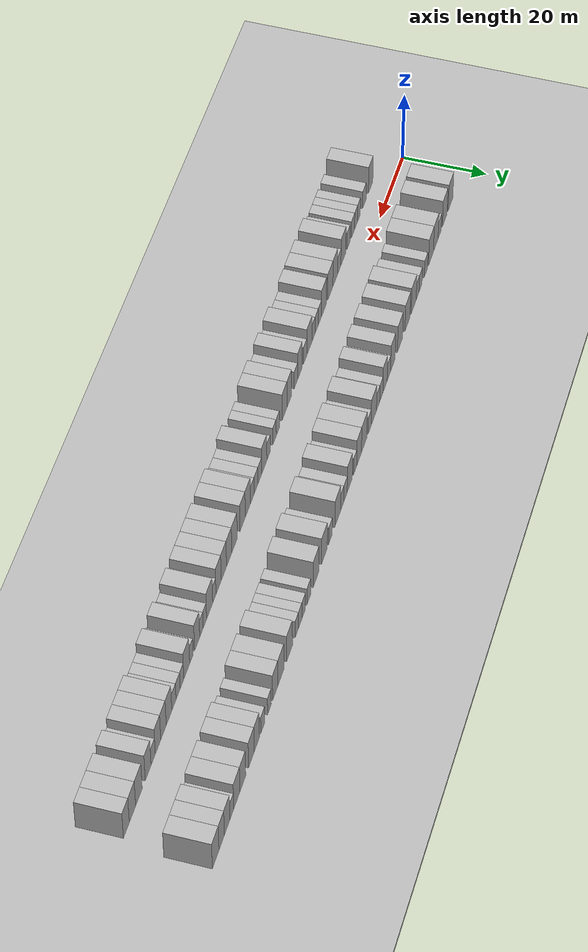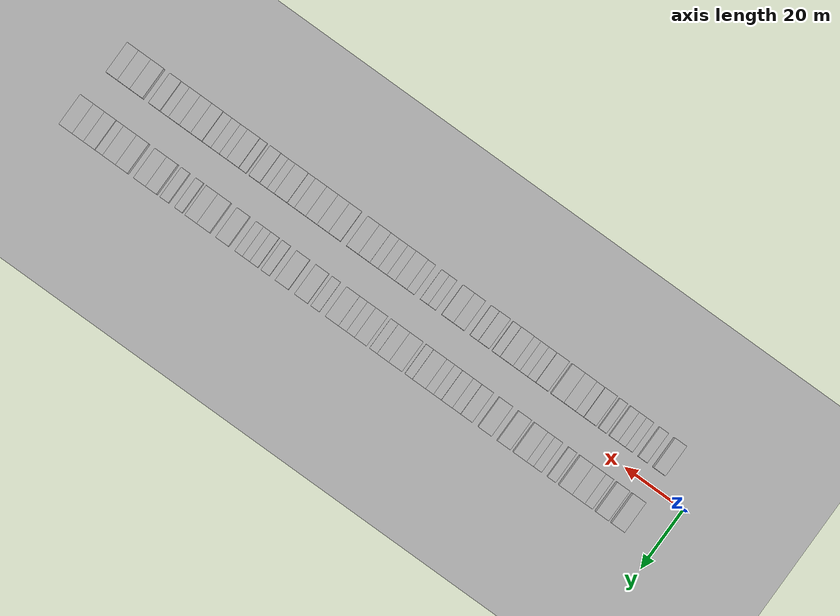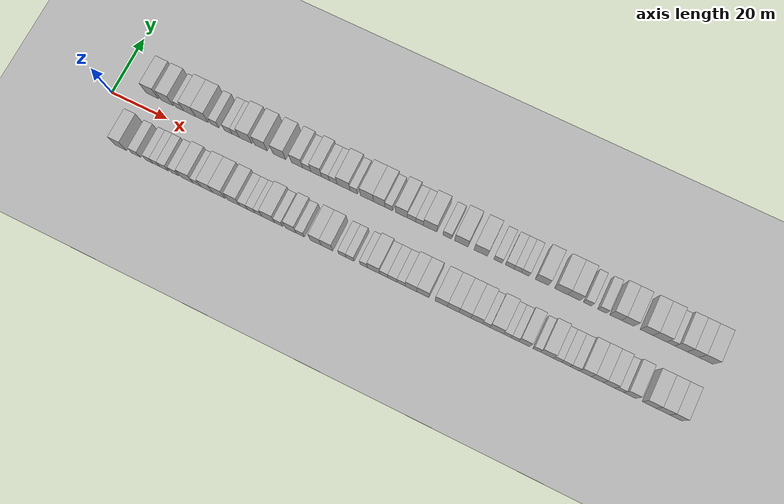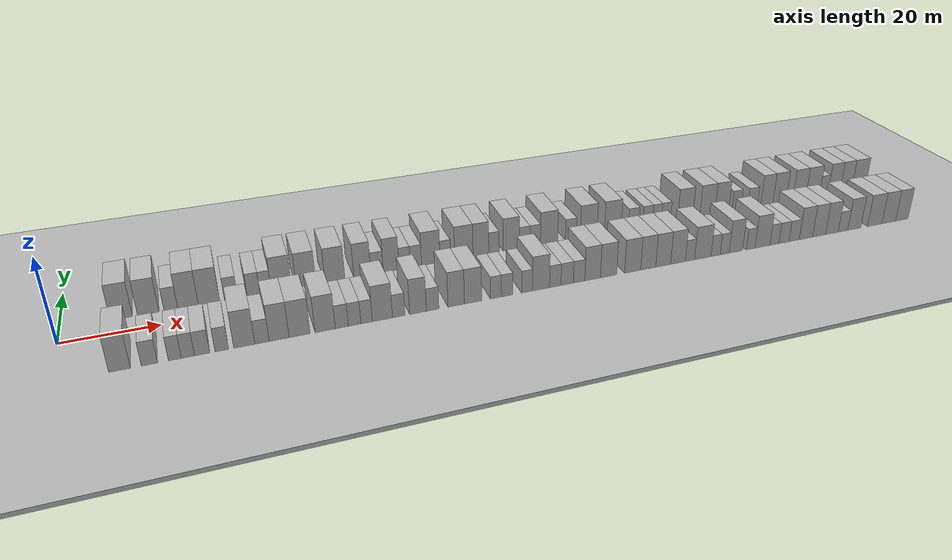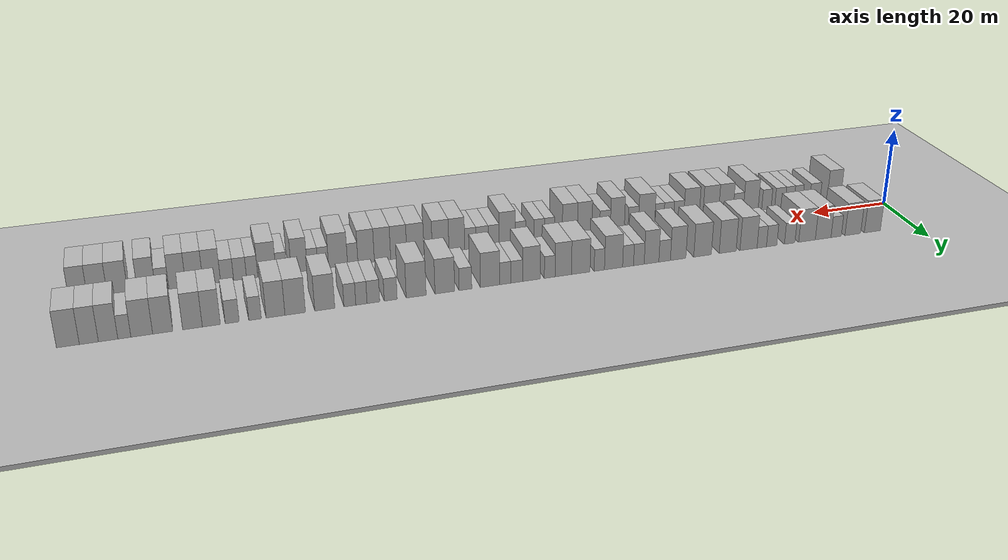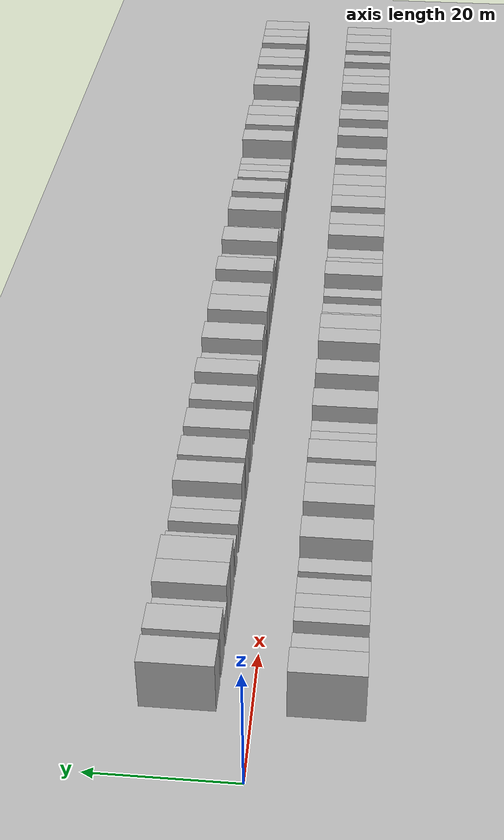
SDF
<?xml version="1.0" encoding="utf-8"?>

<sdf version="1.6">

   <world name="default">

      <gui fullscreen="0">

         <camera name="user_camera">

            <pose>-15 0 4.57585 0 0 0</pose>

            <view_controller>orbit</view_controller>

         </camera>

      </gui>

      <scene>

         <sky>

           <clouds>

             <speed>12</speed>

           </clouds>

         </sky>

         <ambient>0.4 0.4 0.4 1</ambient>

         <background>0.7 0.7 0.7 1</background>

         <shadows>1</shadows>

      </scene>

      <gravity>0 0 -9.8066</gravity>

      <magnetic_field>6e-06 2.3e-05 -4.2e-05</magnetic_field>

      <physics default="0" name="default_physics" type="ode">

         <ode>

            <solver>

               <type>quick</type>

               <iters>10</iters>

               <sor>1.0</sor>

               <use_dynamic_moi_rescaling>0</use_dynamic_moi_rescaling>

            </solver>

            <constraints>

               <cfm>0</cfm>

               <erp>0.2</erp>

               <contact_max_correcting_vel>100</contact_max_correcting_vel>

               <contact_surface_layer>0.001</contact_surface_layer>

            </constraints>

         </ode>

         <max_step_size>0.004</max_step_size>

         <real_time_factor>1</real_time_factor>

         <real_time_update_rate>250</real_time_update_rate>

      </physics>

      <light name="sun" type="directional">

         <cast_shadows>1</cast_shadows>

         <pose>0 0 10 0 0 0</pose>

         <diffuse>0.8 0.8 0.8 1</diffuse>

         <specular>0.2 0.2 0.2 1</specular>

         <attenuation>

            <range>1000</range>

            <constant>0.9</constant>

            <linear>0.01</linear>

            <quadratic>0.001</quadratic>

         </attenuation>

         <direction>-0.5 0.1 -0.9</direction>

      </light>

      <include>

         <name>ground_plane_1</name>

         <uri>model://HANNAS_ground_plane</uri>

         <pose>0 0 0  0 0 0</pose>

      </include>

      <include>

         <name>ground_plane_2</name>

         <uri>model://HANNAS_ground_plane</uri>

         <pose>100 0 0  0 0 0</pose>

      </include>

      <model name="building_1">

         <static>1</static>

         <pose frame="">12.1943 9.5000 0 0.000000 0.000000 1.570796</pose>

         <link name="link">

            <pose frame="">0 0 4.50 0 0 0</pose>

            <collision name="collision">

               <geometry>

                  <box>

                     <size>10.0000 4.3886 9.0000</size>

                  </box>

               </geometry>

               <max_contacts>10</max_contacts>

               <surface>

                  <contact>

                     <ode/>

                  </contact>

                  <bounce/>

                  <friction>

                     <torsional>

                        <ode/>

                     </torsional>

                     <ode/>

                  </friction>

               </surface>

            </collision>

            <visual name="visual">

               <cast_shadows>0</cast_shadows>

               <geometry>

                  <box>

                     <size>10.0000 4.3886 9.0000</size>

                  </box>

               </geometry>

               <material>

                  <script>

                     <uri>model://HANNAS_wall/materials/scripts</uri>

                     <uri>model://HANNAS_wall/materials/textures</uri>

                     <name>vrc/HANNAS_wall</name>

                  </script>

               </material>

            </visual>

            <self_collide>0</self_collide>

            <enable_wind>0</enable_wind>

            <kinematic>0</kinematic>

         </link>

      </model>

      <model name="building_2">

         <static>1</static>

         <pose frame="">17.5279 9.5000 0 0.000000 0.000000 1.570796</pose>

         <link name="link">

            <pose frame="">0 0 4.50 0 0 0</pose>

            <collision name="collision">

               <geometry>

                  <box>

                     <size>10.0000 4.2786 9.0000</size>

                  </box>

               </geometry>

               <max_contacts>10</max_contacts>

               <surface>

                  <contact>

                     <ode/>

                  </contact>

                  <bounce/>

                  <friction>

                     <torsional>

                        <ode/>

                     </torsional>

                     <ode/>

                  </friction>

               </surface>

            </collision>

            <visual name="visual">

               <cast_shadows>0</cast_shadows>

               <geometry>

                  <box>

                     <size>10.0000 4.2786 9.0000</size>

                  </box>

               </geometry>

               <material>

                  <script>

                     <uri>model://HANNAS_wall/materials/scripts</uri>

                     <uri>model://HANNAS_wall/materials/textures</uri>

                     <name>vrc/HANNAS_wall</name>

                  </script>

               </material>

            </visual>

            <self_collide>0</self_collide>

            <enable_wind>0</enable_wind>

            <kinematic>0</kinematic>

         </link>

      </model>

      <model name="building_3">

         <static>1</static>

         <pose frame="">22.0547 9.5000 0 0.000000 0.000000 1.570796</pose>

         <link name="link">

            <pose frame="">0 0 3.00 0 0 0</pose>

            <collision name="collision">

               <geometry>

                  <box>

                     <size>10.0000 2.7752 6.0000</size>

                  </box>

               </geometry>

               <max_contacts>10</max_contacts>

               <surface>

                  <contact>

                     <ode/>

                  </contact>

                  <bounce/>

                  <friction>

                     <torsional>

                        <ode/>

                     </torsional>

                     <ode/>

                  </friction>

               </surface>

            </collision>

            <visual name="visual">

               <cast_shadows>0</cast_shadows>

               <geometry>

                  <box>

                     <size>10.0000 2.7752 6.0000</size>

                  </box>

               </geometry>

               <material>

                  <script>

                     <uri>model://HANNAS_wall/materials/scripts</uri>

                     <uri>model://HANNAS_wall/materials/textures</uri>

                     <name>vrc/HANNAS_wall</name>

                  </script>

               </material>

            </visual>

            <self_collide>0</self_collide>

            <enable_wind>0</enable_wind>

            <kinematic>0</kinematic>

         </link>

      </model>

      <model name="building_4">

         <static>1</static>

         <pose frame="">25.5473 9.5000 0 0.000000 0.000000 1.570796</pose>

         <link name="link">

            <pose frame="">0 0 4.50 0 0 0</pose>

            <collision name="collision">

               <geometry>

                  <box>

                     <size>10.0000 4.2099 9.0000</size>

                  </box>

               </geometry>

               <max_contacts>10</max_contacts>

               <surface>

                  <contact>

                     <ode/>

                  </contact>

                  <bounce/>

                  <friction>

                     <torsional>

                        <ode/>

                     </torsional>

                     <ode/>

                  </friction>

               </surface>

            </collision>

            <visual name="visual">

               <cast_shadows>0</cast_shadows>

               <geometry>

                  <box>

                     <size>10.0000 4.2099 9.0000</size>

                  </box>

               </geometry>

               <material>

                  <script>

                     <uri>model://HANNAS_wall/materials/scripts</uri>

                     <uri>model://HANNAS_wall/materials/textures</uri>

                     <name>vrc/HANNAS_wall</name>

                  </script>

               </material>

            </visual>

            <self_collide>0</self_collide>

            <enable_wind>0</enable_wind>

            <kinematic>0</kinematic>

         </link>

      </model>

      <model name="building_5">

         <static>1</static>

         <pose frame="">29.8634 9.5000 0 0.000000 0.000000 1.570796</pose>

         <link name="link">

            <pose frame="">0 0 4.50 0 0 0</pose>

            <collision name="collision">

               <geometry>

                  <box>

                     <size>10.0000 4.4223 9.0000</size>

                  </box>

               </geometry>

               <max_contacts>10</max_contacts>

               <surface>

                  <contact>

                     <ode/>

                  </contact>

                  <bounce/>

                  <friction>

                     <torsional>

                        <ode/>

                     </torsional>

                     <ode/>

                  </friction>

               </surface>

            </collision>

            <visual name="visual">

               <cast_shadows>0</cast_shadows>

               <geometry>

                  <box>

                     <size>10.0000 4.4223 9.0000</size>

                  </box>

               </geometry>

               <material>

                  <script>

                     <uri>model://HANNAS_wall/materials/scripts</uri>

                     <uri>model://HANNAS_wall/materials/textures</uri>

                     <name>vrc/HANNAS_wall</name>

                  </script>

               </material>

            </visual>

            <self_collide>0</self_collide>

            <enable_wind>0</enable_wind>

            <kinematic>0</kinematic>

         </link>

      </model>

      <model name="building_6">

         <static>1</static>

         <pose frame="">34.4579 9.5000 0 0.000000 0.000000 1.570796</pose>

         <link name="link">

            <pose frame="">0 0 3.00 0 0 0</pose>

            <collision name="collision">

               <geometry>

                  <box>

                     <size>10.0000 2.7668 6.0000</size>

                  </box>

               </geometry>

               <max_contacts>10</max_contacts>

               <surface>

                  <contact>

                     <ode/>

                  </contact>

                  <bounce/>

                  <friction>

                     <torsional>

                        <ode/>

                     </torsional>

                     <ode/>

                  </friction>

               </surface>

            </collision>

            <visual name="visual">

               <cast_shadows>0</cast_shadows>

               <geometry>

                  <box>

                     <size>10.0000 2.7668 6.0000</size>

                  </box>

               </geometry>

               <material>

                  <script>

                     <uri>model://HANNAS_wall/materials/scripts</uri>

                     <uri>model://HANNAS_wall/materials/textures</uri>

                     <name>vrc/HANNAS_wall</name>

                  </script>

               </material>

            </visual>

            <self_collide>0</self_collide>

            <enable_wind>0</enable_wind>

            <kinematic>0</kinematic>

         </link>

      </model>

      <model name="building_7">

         <static>1</static>

         <pose frame="">39.2007 9.5000 0 0.000000 0.000000 1.570796</pose>

         <link name="link">

            <pose frame="">0 0 3.00 0 0 0</pose>

            <collision name="collision">

               <geometry>

                  <box>

                     <size>10.0000 2.7189 6.0000</size>

                  </box>

               </geometry>

               <max_contacts>10</max_contacts>

               <surface>

                  <contact>

                     <ode/>

                  </contact>

                  <bounce/>

                  <friction>

                     <torsional>

                        <ode/>

                     </torsional>

                     <ode/>

                  </friction>

               </surface>

            </collision>

            <visual name="visual">

               <cast_shadows>0</cast_shadows>

               <geometry>

                  <box>

                     <size>10.0000 2.7189 6.0000</size>

                  </box>

               </geometry>

               <material>

                  <script>

                     <uri>model://HANNAS_wall/materials/scripts</uri>

                     <uri>model://HANNAS_wall/materials/textures</uri>

                     <name>vrc/HANNAS_wall</name>

                  </script>

               </material>

            </visual>

            <self_collide>0</self_collide>

            <enable_wind>0</enable_wind>

            <kinematic>0</kinematic>

         </link>

      </model>

      <model name="building_8">

         <static>1</static>

         <pose frame="">41.7880 9.5000 0 0.000000 0.000000 1.570796</pose>

         <link name="link">

            <pose frame="">0 0 3.00 0 0 0</pose>

            <collision name="collision">

               <geometry>

                  <box>

                     <size>10.0000 2.4557 6.0000</size>

                  </box>

               </geometry>

               <max_contacts>10</max_contacts>

               <surface>

                  <contact>

                     <ode/>

                  </contact>

                  <bounce/>

                  <friction>

                     <torsional>

                        <ode/>

                     </torsional>

                     <ode/>

                  </friction>

               </surface>

            </collision>

            <visual name="visual">

               <cast_shadows>0</cast_shadows>

               <geometry>

                  <box>

                     <size>10.0000 2.4557 6.0000</size>

                  </box>

               </geometry>

               <material>

                  <script>

                     <uri>model://HANNAS_wall/materials/scripts</uri>

                     <uri>model://HANNAS_wall/materials/textures</uri>

                     <name>vrc/HANNAS_wall</name>

                  </script>

               </material>

            </visual>

            <self_collide>0</self_collide>

            <enable_wind>0</enable_wind>

            <kinematic>0</kinematic>

         </link>

      </model>

      <model name="building_9">

         <static>1</static>

         <pose frame="">45.2294 9.5000 0 0.000000 0.000000 1.570796</pose>

         <link name="link">

            <pose frame="">0 0 4.50 0 0 0</pose>

            <collision name="collision">

               <geometry>

                  <box>

                     <size>10.0000 4.4270 9.0000</size>

                  </box>

               </geometry>

               <max_contacts>10</max_contacts>

               <surface>

                  <contact>

                     <ode/>

                  </contact>

                  <bounce/>

                  <friction>

                     <torsional>

                        <ode/>

                     </torsional>

                     <ode/>

                  </friction>

               </surface>

            </collision>

            <visual name="visual">

               <cast_shadows>0</cast_shadows>

               <geometry>

                  <box>

                     <size>10.0000 4.4270 9.0000</size>

                  </box>

               </geometry>

               <material>

                  <script>

                     <uri>model://HANNAS_wall/materials/scripts</uri>

                     <uri>model://HANNAS_wall/materials/textures</uri>

                     <name>vrc/HANNAS_wall</name>

                  </script>

               </material>

            </visual>

            <self_collide>0</self_collide>

            <enable_wind>0</enable_wind>

            <kinematic>0</kinematic>

         </link>

      </model>

      <model name="building_10">

         <static>1</static>

         <pose frame="">50.6140 9.5000 0 0.000000 0.000000 1.570796</pose>

         <link name="link">

            <pose frame="">0 0 4.50 0 0 0</pose>

            <collision name="collision">

               <geometry>

                  <box>

                     <size>10.0000 4.3423 9.0000</size>

                  </box>

               </geometry>

               <max_contacts>10</max_contacts>

               <surface>

                  <contact>

                     <ode/>

                  </contact>

                  <bounce/>

                  <friction>

                     <torsional>

                        <ode/>

                     </torsional>

                     <ode/>

                  </friction>

               </surface>

            </collision>

            <visual name="visual">

               <cast_shadows>0</cast_shadows>

               <geometry>

                  <box>

                     <size>10.0000 4.3423 9.0000</size>

                  </box>

               </geometry>

               <material>

                  <script>

                     <uri>model://HANNAS_wall/materials/scripts</uri>

                     <uri>model://HANNAS_wall/materials/textures</uri>

                     <name>vrc/HANNAS_wall</name>

                  </script>

               </material>

            </visual>

            <self_collide>0</self_collide>

            <enable_wind>0</enable_wind>

            <kinematic>0</kinematic>

         </link>

      </model>

      <model name="building_11">

         <static>1</static>

         <pose frame="">57.0152 9.5000 0 0.000000 0.000000 1.570796</pose>

         <link name="link">

            <pose frame="">0 0 4.50 0 0 0</pose>

            <collision name="collision">

               <geometry>

                  <box>

                     <size>10.0000 4.4601 9.0000</size>

                  </box>

               </geometry>

               <max_contacts>10</max_contacts>

               <surface>

                  <contact>

                     <ode/>

                  </contact>

                  <bounce/>

                  <friction>

                     <torsional>

                        <ode/>

                     </torsional>

                     <ode/>

                  </friction>

               </surface>

            </collision>

            <visual name="visual">

               <cast_shadows>0</cast_shadows>

               <geometry>

                  <box>

                     <size>10.0000 4.4601 9.0000</size>

                  </box>

               </geometry>

               <material>

                  <script>

                     <uri>model://HANNAS_wall/materials/scripts</uri>

                     <uri>model://HANNAS_wall/materials/textures</uri>

                     <name>vrc/HANNAS_wall</name>

                  </script>

               </material>

            </visual>

            <self_collide>0</self_collide>

            <enable_wind>0</enable_wind>

            <kinematic>0</kinematic>

         </link>

      </model>

      <model name="building_12">

         <static>1</static>

         <pose frame="">63.1867 9.5000 0 0.000000 0.000000 1.570796</pose>

         <link name="link">

            <pose frame="">0 0 4.50 0 0 0</pose>

            <collision name="collision">

               <geometry>

                  <box>

                     <size>10.0000 3.8828 9.0000</size>

                  </box>

               </geometry>

               <max_contacts>10</max_contacts>

               <surface>

                  <contact>

                     <ode/>

                  </contact>

                  <bounce/>

                  <friction>

                     <torsional>

                        <ode/>

                     </torsional>

                     <ode/>

                  </friction>

               </surface>

            </collision>

            <visual name="visual">

               <cast_shadows>0</cast_shadows>

               <geometry>

                  <box>

                     <size>10.0000 3.8828 9.0000</size>

                  </box>

               </geometry>

               <material>

                  <script>

                     <uri>model://HANNAS_wall/materials/scripts</uri>

                     <uri>model://HANNAS_wall/materials/textures</uri>

                     <name>vrc/HANNAS_wall</name>

                  </script>

               </material>

            </visual>

            <self_collide>0</self_collide>

            <enable_wind>0</enable_wind>

            <kinematic>0</kinematic>

         </link>

      </model>

      <model name="building_13">

         <static>1</static>

         <pose frame="">66.5711 9.5000 0 0.000000 0.000000 1.570796</pose>

         <link name="link">

            <pose frame="">0 0 3.00 0 0 0</pose>

            <collision name="collision">

               <geometry>

                  <box>

                     <size>10.0000 2.8859 6.0000</size>

                  </box>

               </geometry>

               <max_contacts>10</max_contacts>

               <surface>

                  <contact>

                     <ode/>

                  </contact>

                  <bounce/>

                  <friction>

                     <torsional>

                        <ode/>

                     </torsional>

                     <ode/>

                  </friction>

               </surface>

            </collision>

            <visual name="visual">

               <cast_shadows>0</cast_shadows>

               <geometry>

                  <box>

                     <size>10.0000 2.8859 6.0000</size>

                  </box>

               </geometry>

               <material>

                  <script>

                     <uri>model://HANNAS_wall/materials/scripts</uri>

                     <uri>model://HANNAS_wall/materials/textures</uri>

                     <name>vrc/HANNAS_wall</name>

                  </script>

               </material>

            </visual>

            <self_collide>0</self_collide>

            <enable_wind>0</enable_wind>

            <kinematic>0</kinematic>

         </link>

      </model>

      <model name="building_14">

         <static>1</static>

         <pose frame="">69.8348 9.5000 0 0.000000 0.000000 1.570796</pose>

         <link name="link">

            <pose frame="">0 0 4.50 0 0 0</pose>

            <collision name="collision">

               <geometry>

                  <box>

                     <size>10.0000 3.6416 9.0000</size>

                  </box>

               </geometry>

               <max_contacts>10</max_contacts>

               <surface>

                  <contact>

                     <ode/>

                  </contact>

                  <bounce/>

                  <friction>

                     <torsional>

                        <ode/>

                     </torsional>

                     <ode/>

                  </friction>

               </surface>

            </collision>

            <visual name="visual">

               <cast_shadows>0</cast_shadows>

               <geometry>

                  <box>

                     <size>10.0000 3.6416 9.0000</size>

                  </box>

               </geometry>

               <material>

                  <script>

                     <uri>model://HANNAS_wall/materials/scripts</uri>

                     <uri>model://HANNAS_wall/materials/textures</uri>

                     <name>vrc/HANNAS_wall</name>

                  </script>

               </material>

            </visual>

            <self_collide>0</self_collide>

            <enable_wind>0</enable_wind>

            <kinematic>0</kinematic>

         </link>

      </model>

      <model name="building_15">

         <static>1</static>

         <pose frame="">72.9685 9.5000 0 0.000000 0.000000 1.570796</pose>

         <link name="link">

            <pose frame="">0 0 3.00 0 0 0</pose>

            <collision name="collision">

               <geometry>

                  <box>

                     <size>10.0000 2.6257 6.0000</size>

                  </box>

               </geometry>

               <max_contacts>10</max_contacts>

               <surface>

                  <contact>

                     <ode/>

                  </contact>

                  <bounce/>

                  <friction>

                     <torsional>

                        <ode/>

                     </torsional>

                     <ode/>

                  </friction>

               </surface>

            </collision>

            <visual name="visual">

               <cast_shadows>0</cast_shadows>

               <geometry>

                  <box>

                     <size>10.0000 2.6257 6.0000</size>

                  </box>

               </geometry>

               <material>

                  <script>

                     <uri>model://HANNAS_wall/materials/scripts</uri>

                     <uri>model://HANNAS_wall/materials/textures</uri>

                     <name>vrc/HANNAS_wall</name>

                  </script>

               </material>

            </visual>

            <self_collide>0</self_collide>

            <enable_wind>0</enable_wind>

            <kinematic>0</kinematic>

         </link>

      </model>

      <model name="building_16">

         <static>1</static>

         <pose frame="">75.6257 9.5000 0 0.000000 0.000000 1.570796</pose>

         <link name="link">

            <pose frame="">0 0 3.00 0 0 0</pose>

            <collision name="collision">

               <geometry>

                  <box>

                     <size>10.0000 2.6889 6.0000</size>

                  </box>

               </geometry>

               <max_contacts>10</max_contacts>

               <surface>

                  <contact>

                     <ode/>

                  </contact>

                  <bounce/>

                  <friction>

                     <torsional>

                        <ode/>

                     </torsional>

                     <ode/>

                  </friction>

               </surface>

            </collision>

            <visual name="visual">

               <cast_shadows>0</cast_shadows>

               <geometry>

                  <box>

                     <size>10.0000 2.6889 6.0000</size>

                  </box>

               </geometry>

               <material>

                  <script>

                     <uri>model://HANNAS_wall/materials/scripts</uri>

                     <uri>model://HANNAS_wall/materials/textures</uri>

                     <name>vrc/HANNAS_wall</name>

                  </script>

               </material>

            </visual>

            <self_collide>0</self_collide>

            <enable_wind>0</enable_wind>

            <kinematic>0</kinematic>

         </link>

      </model>

      <model name="building_17">

         <static>1</static>

         <pose frame="">79.1832 9.5000 0 0.000000 0.000000 1.570796</pose>

         <link name="link">

            <pose frame="">0 0 4.50 0 0 0</pose>

            <collision name="collision">

               <geometry>

                  <box>

                     <size>10.0000 4.4260 9.0000</size>

                  </box>

               </geometry>

               <max_contacts>10</max_contacts>

               <surface>

                  <contact>

                     <ode/>

                  </contact>

                  <bounce/>

                  <friction>

                     <torsional>

                        <ode/>

                     </torsional>

                     <ode/>

                  </friction>

               </surface>

            </collision>

            <visual name="visual">

               <cast_shadows>0</cast_shadows>

               <geometry>

                  <box>

                     <size>10.0000 4.4260 9.0000</size>

                  </box>

               </geometry>

               <material>

                  <script>

                     <uri>model://HANNAS_wall/materials/scripts</uri>

                     <uri>model://HANNAS_wall/materials/textures</uri>

                     <name>vrc/HANNAS_wall</name>

                  </script>

               </material>

            </visual>

            <self_collide>0</self_collide>

            <enable_wind>0</enable_wind>

            <kinematic>0</kinematic>

         </link>

      </model>

      <model name="building_18">

         <static>1</static>

         <pose frame="">82.6501 9.5000 0 0.000000 0.000000 1.570796</pose>

         <link name="link">

            <pose frame="">0 0 3.00 0 0 0</pose>

            <collision name="collision">

               <geometry>

                  <box>

                     <size>10.0000 2.5079 6.0000</size>

                  </box>

               </geometry>

               <max_contacts>10</max_contacts>

               <surface>

                  <contact>

                     <ode/>

                  </contact>

                  <bounce/>

                  <friction>

                     <torsional>

                        <ode/>

                     </torsional>

                     <ode/>

                  </friction>

               </surface>

            </collision>

            <visual name="visual">

               <cast_shadows>0</cast_shadows>

               <geometry>

                  <box>

                     <size>10.0000 2.5079 6.0000</size>

                  </box>

               </geometry>

               <material>

                  <script>

                     <uri>model://HANNAS_wall/materials/scripts</uri>

                     <uri>model://HANNAS_wall/materials/textures</uri>

                     <name>vrc/HANNAS_wall</name>

                  </script>

               </material>

            </visual>

            <self_collide>0</self_collide>

            <enable_wind>0</enable_wind>

            <kinematic>0</kinematic>

         </link>

      </model>

      <model name="building_19">

         <static>1</static>

         <pose frame="">87.1406 9.5000 0 0.000000 0.000000 1.570796</pose>

         <link name="link">

            <pose frame="">0 0 4.50 0 0 0</pose>

            <collision name="collision">

               <geometry>

                  <box>

                     <size>10.0000 4.4731 9.0000</size>

                  </box>

               </geometry>

               <max_contacts>10</max_contacts>

               <surface>

                  <contact>

                     <ode/>

                  </contact>

                  <bounce/>

                  <friction>

                     <torsional>

                        <ode/>

                     </torsional>

                     <ode/>

                  </friction>

               </surface>

            </collision>

            <visual name="visual">

               <cast_shadows>0</cast_shadows>

               <geometry>

                  <box>

                     <size>10.0000 4.4731 9.0000</size>

                  </box>

               </geometry>

               <material>

                  <script>

                     <uri>model://HANNAS_wall/materials/scripts</uri>

                     <uri>model://HANNAS_wall/materials/textures</uri>

                     <name>vrc/HANNAS_wall</name>

                  </script>

               </material>

            </visual>

            <self_collide>0</self_collide>

            <enable_wind>0</enable_wind>

            <kinematic>0</kinematic>

         </link>

      </model>

      <model name="building_20">

         <static>1</static>

         <pose frame="">91.3260 9.5000 0 0.000000 0.000000 1.570796</pose>

         <link name="link">

            <pose frame="">0 0 4.50 0 0 0</pose>

            <collision name="collision">

               <geometry>

                  <box>

                     <size>10.0000 3.8978 9.0000</size>

                  </box>

               </geometry>

               <max_contacts>10</max_contacts>

               <surface>

                  <contact>

                     <ode/>

                  </contact>

                  <bounce/>

                  <friction>

                     <torsional>

                        <ode/>

                     </torsional>

                     <ode/>

                  </friction>

               </surface>

            </collision>

            <visual name="visual">

               <cast_shadows>0</cast_shadows>

               <geometry>

                  <box>

                     <size>10.0000 3.8978 9.0000</size>

                  </box>

               </geometry>

               <material>

                  <script>

                     <uri>model://HANNAS_wall/materials/scripts</uri>

                     <uri>model://HANNAS_wall/materials/textures</uri>

                     <name>vrc/HANNAS_wall</name>

                  </script>

               </material>

            </visual>

            <self_collide>0</self_collide>

            <enable_wind>0</enable_wind>

            <kinematic>0</kinematic>

         </link>

      </model>

      <model name="building_21">

         <static>1</static>

         <pose frame="">94.5484 9.5000 0 0.000000 0.000000 1.570796</pose>

         <link name="link">

            <pose frame="">0 0 3.00 0 0 0</pose>

            <collision name="collision">

               <geometry>

                  <box>

                     <size>10.0000 2.5469 6.0000</size>

                  </box>

               </geometry>

               <max_contacts>10</max_contacts>

               <surface>

                  <contact>

                     <ode/>

                  </contact>

                  <bounce/>

                  <friction>

                     <torsional>

                        <ode/>

                     </torsional>

                     <ode/>

                  </friction>

               </surface>

            </collision>

            <visual name="visual">

               <cast_shadows>0</cast_shadows>

               <geometry>

                  <box>

                     <size>10.0000 2.5469 6.0000</size>

                  </box>

               </geometry>

               <material>

                  <script>

                     <uri>model://HANNAS_wall/materials/scripts</uri>

                     <uri>model://HANNAS_wall/materials/textures</uri>

                     <name>vrc/HANNAS_wall</name>

                  </script>

               </material>

            </visual>

            <self_collide>0</self_collide>

            <enable_wind>0</enable_wind>

            <kinematic>0</kinematic>

         </link>

      </model>

      <model name="building_22">

         <static>1</static>

         <pose frame="">98.8495 9.5000 0 0.000000 0.000000 1.570796</pose>

         <link name="link">

            <pose frame="">0 0 4.50 0 0 0</pose>

            <collision name="collision">

               <geometry>

                  <box>

                     <size>10.0000 4.0554 9.0000</size>

                  </box>

               </geometry>

               <max_contacts>10</max_contacts>

               <surface>

                  <contact>

                     <ode/>

                  </contact>

                  <bounce/>

                  <friction>

                     <torsional>

                        <ode/>

                     </torsional>

                     <ode/>

                  </friction>

               </surface>

            </collision>

            <visual name="visual">

               <cast_shadows>0</cast_shadows>

               <geometry>

                  <box>

                     <size>10.0000 4.0554 9.0000</size>

                  </box>

               </geometry>

               <material>

                  <script>

                     <uri>model://HANNAS_wall/materials/scripts</uri>

                     <uri>model://HANNAS_wall/materials/textures</uri>

                     <name>vrc/HANNAS_wall</name>

                  </script>

               </material>

            </visual>

            <self_collide>0</self_collide>

            <enable_wind>0</enable_wind>

            <kinematic>0</kinematic>

         </link>

      </model>

      <model name="building_23">

         <static>1</static>

         <pose frame="">102.2516 9.5000 0 0.000000 0.000000 1.570796</pose>

         <link name="link">

            <pose frame="">0 0 3.00 0 0 0</pose>

            <collision name="collision">

               <geometry>

                  <box>

                     <size>10.0000 2.7488 6.0000</size>

                  </box>

               </geometry>

               <max_contacts>10</max_contacts>

               <surface>

                  <contact>

                     <ode/>

                  </contact>

                  <bounce/>

                  <friction>

                     <torsional>

                        <ode/>

                     </torsional>

                     <ode/>

                  </friction>

               </surface>

            </collision>

            <visual name="visual">

               <cast_shadows>0</cast_shadows>

               <geometry>

                  <box>

                     <size>10.0000 2.7488 6.0000</size>

                  </box>

               </geometry>

               <material>

                  <script>

                     <uri>model://HANNAS_wall/materials/scripts</uri>

                     <uri>model://HANNAS_wall/materials/textures</uri>

                     <name>vrc/HANNAS_wall</name>

                  </script>

               </material>

            </visual>

            <self_collide>0</self_collide>

            <enable_wind>0</enable_wind>

            <kinematic>0</kinematic>

         </link>

      </model>

      <model name="building_24">

         <static>1</static>

         <pose frame="">104.9488 9.5000 0 0.000000 0.000000 1.570796</pose>

         <link name="link">

            <pose frame="">0 0 3.00 0 0 0</pose>

            <collision name="collision">

               <geometry>

                  <box>

                     <size>10.0000 2.6455 6.0000</size>

                  </box>

               </geometry>

               <max_contacts>10</max_contacts>

               <surface>

                  <contact>

                     <ode/>

                  </contact>

                  <bounce/>

                  <friction>

                     <torsional>

                        <ode/>

                     </torsional>

                     <ode/>

                  </friction>

               </surface>

            </collision>

            <visual name="visual">

               <cast_shadows>0</cast_shadows>

               <geometry>

                  <box>

                     <size>10.0000 2.6455 6.0000</size>

                  </box>

               </geometry>

               <material>

                  <script>

                     <uri>model://HANNAS_wall/materials/scripts</uri>

                     <uri>model://HANNAS_wall/materials/textures</uri>

                     <name>vrc/HANNAS_wall</name>

                  </script>

               </material>

            </visual>

            <self_collide>0</self_collide>

            <enable_wind>0</enable_wind>

            <kinematic>0</kinematic>

         </link>

      </model>

      <model name="building_25">

         <static>1</static>

         <pose frame="">108.4998 9.5000 0 0.000000 0.000000 1.570796</pose>

         <link name="link">

            <pose frame="">0 0 4.50 0 0 0</pose>

            <collision name="collision">

               <geometry>

                  <box>

                     <size>10.0000 4.4565 9.0000</size>

                  </box>

               </geometry>

               <max_contacts>10</max_contacts>

               <surface>

                  <contact>

                     <ode/>

                  </contact>

                  <bounce/>

                  <friction>

                     <torsional>

                        <ode/>

                     </torsional>

                     <ode/>

                  </friction>

               </surface>

            </collision>

            <visual name="visual">

               <cast_shadows>0</cast_shadows>

               <geometry>

                  <box>

                     <size>10.0000 4.4565 9.0000</size>

                  </box>

               </geometry>

               <material>

                  <script>

                     <uri>model://HANNAS_wall/materials/scripts</uri>

                     <uri>model://HANNAS_wall/materials/textures</uri>

                     <name>vrc/HANNAS_wall</name>

                  </script>

               </material>

            </visual>

            <self_collide>0</self_collide>

            <enable_wind>0</enable_wind>

            <kinematic>0</kinematic>

         </link>

      </model>

      <model name="building_26">

         <static>1</static>

         <pose frame="">114.1830 9.5000 0 0.000000 0.000000 1.570796</pose>

         <link name="link">

            <pose frame="">0 0 3.00 0 0 0</pose>

            <collision name="collision">

               <geometry>

                  <box>

                     <size>10.0000 2.9098 6.0000</size>

                  </box>

               </geometry>

               <max_contacts>10</max_contacts>

               <surface>

                  <contact>

                     <ode/>

                  </contact>

                  <bounce/>

                  <friction>

                     <torsional>

                        <ode/>

                     </torsional>

                     <ode/>

                  </friction>

               </surface>

            </collision>

            <visual name="visual">

               <cast_shadows>0</cast_shadows>

               <geometry>

                  <box>

                     <size>10.0000 2.9098 6.0000</size>

                  </box>

               </geometry>

               <material>

                  <script>

                     <uri>model://HANNAS_wall/materials/scripts</uri>

                     <uri>model://HANNAS_wall/materials/textures</uri>

                     <name>vrc/HANNAS_wall</name>

                  </script>

               </material>

            </visual>

            <self_collide>0</self_collide>

            <enable_wind>0</enable_wind>

            <kinematic>0</kinematic>

         </link>

      </model>

      <model name="building_27">

         <static>1</static>

         <pose frame="">118.8690 9.5000 0 0.000000 0.000000 1.570796</pose>

         <link name="link">

            <pose frame="">0 0 4.50 0 0 0</pose>

            <collision name="collision">

               <geometry>

                  <box>

                     <size>10.0000 4.4622 9.0000</size>

                  </box>

               </geometry>

               <max_contacts>10</max_contacts>

               <surface>

                  <contact>

                     <ode/>

                  </contact>

                  <bounce/>

                  <friction>

                     <torsional>

                        <ode/>

                     </torsional>

                     <ode/>

                  </friction>

               </surface>

            </collision>

            <visual name="visual">

               <cast_shadows>0</cast_shadows>

               <geometry>

                  <box>

                     <size>10.0000 4.4622 9.0000</size>

                  </box>

               </geometry>

               <material>

                  <script>

                     <uri>model://HANNAS_wall/materials/scripts</uri>

                     <uri>model://HANNAS_wall/materials/textures</uri>

                     <name>vrc/HANNAS_wall</name>

                  </script>

               </material>

            </visual>

            <self_collide>0</self_collide>

            <enable_wind>0</enable_wind>

            <kinematic>0</kinematic>

         </link>

      </model>

      <model name="building_28">

         <static>1</static>

         <pose frame="">125.3372 9.5000 0 0.000000 0.000000 1.570796</pose>

         <link name="link">

            <pose frame="">0 0 4.50 0 0 0</pose>

            <collision name="collision">

               <geometry>

                  <box>

                     <size>10.0000 4.4742 9.0000</size>

                  </box>

               </geometry>

               <max_contacts>10</max_contacts>

               <surface>

                  <contact>

                     <ode/>

                  </contact>

                  <bounce/>

                  <friction>

                     <torsional>

                        <ode/>

                     </torsional>

                     <ode/>

                  </friction>

               </surface>

            </collision>

            <visual name="visual">

               <cast_shadows>0</cast_shadows>

               <geometry>

                  <box>

                     <size>10.0000 4.4742 9.0000</size>

                  </box>

               </geometry>

               <material>

                  <script>

                     <uri>model://HANNAS_wall/materials/scripts</uri>

                     <uri>model://HANNAS_wall/materials/textures</uri>

                     <name>vrc/HANNAS_wall</name>

                  </script>

               </material>

            </visual>

            <self_collide>0</self_collide>

            <enable_wind>0</enable_wind>

            <kinematic>0</kinematic>

         </link>

      </model>

      <model name="building_29">

         <static>1</static>

         <pose frame="">131.0073 9.5000 0 0.000000 0.000000 1.570796</pose>

         <link name="link">

            <pose frame="">0 0 3.00 0 0 0</pose>

            <collision name="collision">

               <geometry>

                  <box>

                     <size>10.0000 2.8662 6.0000</size>

                  </box>

               </geometry>

               <max_contacts>10</max_contacts>

               <surface>

                  <contact>

                     <ode/>

                  </contact>

                  <bounce/>

                  <friction>

                     <torsional>

                        <ode/>

                     </torsional>

                     <ode/>

                  </friction>

               </surface>

            </collision>

            <visual name="visual">

               <cast_shadows>0</cast_shadows>

               <geometry>

                  <box>

                     <size>10.0000 2.8662 6.0000</size>

                  </box>

               </geometry>

               <material>

                  <script>

                     <uri>model://HANNAS_wall/materials/scripts</uri>

                     <uri>model://HANNAS_wall/materials/textures</uri>

                     <name>vrc/HANNAS_wall</name>

                  </script>

               </material>

            </visual>

            <self_collide>0</self_collide>

            <enable_wind>0</enable_wind>

            <kinematic>0</kinematic>

         </link>

      </model>

      <model name="building_30">

         <static>1</static>

         <pose frame="">134.8333 9.5000 0 0.000000 0.000000 1.570796</pose>

         <link name="link">

            <pose frame="">0 0 3.00 0 0 0</pose>

            <collision name="collision">

               <geometry>

                  <box>

                     <size>10.0000 2.7858 6.0000</size>

                  </box>

               </geometry>

               <max_contacts>10</max_contacts>

               <surface>

                  <contact>

                     <ode/>

                  </contact>

                  <bounce/>

                  <friction>

                     <torsional>

                        <ode/>

                     </torsional>

                     <ode/>

                  </friction>

               </surface>

            </collision>

            <visual name="visual">

               <cast_shadows>0</cast_shadows>

               <geometry>

                  <box>

                     <size>10.0000 2.7858 6.0000</size>

                  </box>

               </geometry>

               <material>

                  <script>

                     <uri>model://HANNAS_wall/materials/scripts</uri>

                     <uri>model://HANNAS_wall/materials/textures</uri>

                     <name>vrc/HANNAS_wall</name>

                  </script>

               </material>

            </visual>

            <self_collide>0</self_collide>

            <enable_wind>0</enable_wind>

            <kinematic>0</kinematic>

         </link>

      </model>

      <model name="building_31">

         <static>1</static>

         <pose frame="">137.4578 9.5000 0 0.000000 0.000000 1.570796</pose>

         <link name="link">

            <pose frame="">0 0 3.00 0 0 0</pose>

            <collision name="collision">

               <geometry>

                  <box>

                     <size>10.0000 2.4632 6.0000</size>

                  </box>

               </geometry>

               <max_contacts>10</max_contacts>

               <surface>

                  <contact>

                     <ode/>

                  </contact>

                  <bounce/>

                  <friction>

                     <torsional>

                        <ode/>

                     </torsional>

                     <ode/>

                  </friction>

               </surface>

            </collision>

            <visual name="visual">

               <cast_shadows>0</cast_shadows>

               <geometry>

                  <box>

                     <size>10.0000 2.4632 6.0000</size>

                  </box>

               </geometry>

               <material>

                  <script>

                     <uri>model://HANNAS_wall/materials/scripts</uri>

                     <uri>model://HANNAS_wall/materials/textures</uri>

                     <name>vrc/HANNAS_wall</name>

                  </script>

               </material>

            </visual>

            <self_collide>0</self_collide>

            <enable_wind>0</enable_wind>

            <kinematic>0</kinematic>

         </link>

      </model>

      <model name="building_32">

         <static>1</static>

         <pose frame="">139.9773 9.5000 0 0.000000 0.000000 1.570796</pose>

         <link name="link">

            <pose frame="">0 0 3.00 0 0 0</pose>

            <collision name="collision">

               <geometry>

                  <box>

                     <size>10.0000 2.5758 6.0000</size>

                  </box>

               </geometry>

               <max_contacts>10</max_contacts>

               <surface>

                  <contact>

                     <ode/>

                  </contact>

                  <bounce/>

                  <friction>

                     <torsional>

                        <ode/>

                     </torsional>

                     <ode/>

                  </friction>

               </surface>

            </collision>

            <visual name="visual">

               <cast_shadows>0</cast_shadows>

               <geometry>

                  <box>

                     <size>10.0000 2.5758 6.0000</size>

                  </box>

               </geometry>

               <material>

                  <script>

                     <uri>model://HANNAS_wall/materials/scripts</uri>

                     <uri>model://HANNAS_wall/materials/textures</uri>

                     <name>vrc/HANNAS_wall</name>

                  </script>

               </material>

            </visual>

            <self_collide>0</self_collide>

            <enable_wind>0</enable_wind>

            <kinematic>0</kinematic>

         </link>

      </model>

      <model name="building_33">

         <static>1</static>

         <pose frame="">145.4262 9.5000 0 0.000000 0.000000 1.570796</pose>

         <link name="link">

            <pose frame="">0 0 4.50 0 0 0</pose>

            <collision name="collision">

               <geometry>

                  <box>

                     <size>10.0000 4.3219 9.0000</size>

                  </box>

               </geometry>

               <max_contacts>10</max_contacts>

               <surface>

                  <contact>

                     <ode/>

                  </contact>

                  <bounce/>

                  <friction>

                     <torsional>

                        <ode/>

                     </torsional>

                     <ode/>

                  </friction>

               </surface>

            </collision>

            <visual name="visual">

               <cast_shadows>0</cast_shadows>

               <geometry>

                  <box>

                     <size>10.0000 4.3219 9.0000</size>

                  </box>

               </geometry>

               <material>

                  <script>

                     <uri>model://HANNAS_wall/materials/scripts</uri>

                     <uri>model://HANNAS_wall/materials/textures</uri>

                     <name>vrc/HANNAS_wall</name>

                  </script>

               </material>

            </visual>

            <self_collide>0</self_collide>

            <enable_wind>0</enable_wind>

            <kinematic>0</kinematic>

         </link>

      </model>

      <model name="building_34">

         <static>1</static>

         <pose frame="">151.7672 9.5000 0 0.000000 0.000000 1.570796</pose>

         <link name="link">

            <pose frame="">0 0 4.50 0 0 0</pose>

            <collision name="collision">

               <geometry>

                  <box>

                     <size>10.0000 4.3601 9.0000</size>

                  </box>

               </geometry>

               <max_contacts>10</max_contacts>

               <surface>

                  <contact>

                     <ode/>

                  </contact>

                  <bounce/>

                  <friction>

                     <torsional>

                        <ode/>

                     </torsional>

                     <ode/>

                  </friction>

               </surface>

            </collision>

            <visual name="visual">

               <cast_shadows>0</cast_shadows>

               <geometry>

                  <box>

                     <size>10.0000 4.3601 9.0000</size>

                  </box>

               </geometry>

               <material>

                  <script>

                     <uri>model://HANNAS_wall/materials/scripts</uri>

                     <uri>model://HANNAS_wall/materials/textures</uri>

                     <name>vrc/HANNAS_wall</name>

                  </script>

               </material>

            </visual>

            <self_collide>0</self_collide>

            <enable_wind>0</enable_wind>

            <kinematic>0</kinematic>

         </link>

      </model>

      <model name="building_35">

         <static>1</static>

         <pose frame="">155.9429 9.5000 0 0.000000 0.000000 1.570796</pose>

         <link name="link">

            <pose frame="">0 0 4.50 0 0 0</pose>

            <collision name="collision">

               <geometry>

                  <box>

                     <size>10.0000 3.9913 9.0000</size>

                  </box>

               </geometry>

               <max_contacts>10</max_contacts>

               <surface>

                  <contact>

                     <ode/>

                  </contact>

                  <bounce/>

                  <friction>

                     <torsional>

                        <ode/>

                     </torsional>

                     <ode/>

                  </friction>

               </surface>

            </collision>

            <visual name="visual">

               <cast_shadows>0</cast_shadows>

               <geometry>

                  <box>

                     <size>10.0000 3.9913 9.0000</size>

                  </box>

               </geometry>

               <material>

                  <script>

                     <uri>model://HANNAS_wall/materials/scripts</uri>

                     <uri>model://HANNAS_wall/materials/textures</uri>

                     <name>vrc/HANNAS_wall</name>

                  </script>

               </material>

            </visual>

            <self_collide>0</self_collide>

            <enable_wind>0</enable_wind>

            <kinematic>0</kinematic>

         </link>

      </model>

      <model name="building_36">

         <static>1</static>

         <pose frame="">160.2535 9.5000 0 0.000000 0.000000 1.570796</pose>

         <link name="link">

            <pose frame="">0 0 3.00 0 0 0</pose>

            <collision name="collision">

               <geometry>

                  <box>

                     <size>10.0000 2.6299 6.0000</size>

                  </box>

               </geometry>

               <max_contacts>10</max_contacts>

               <surface>

                  <contact>

                     <ode/>

                  </contact>

                  <bounce/>

                  <friction>

                     <torsional>

                        <ode/>

                     </torsional>

                     <ode/>

                  </friction>

               </surface>

            </collision>

            <visual name="visual">

               <cast_shadows>0</cast_shadows>

               <geometry>

                  <box>

                     <size>10.0000 2.6299 6.0000</size>

                  </box>

               </geometry>

               <material>

                  <script>

                     <uri>model://HANNAS_wall/materials/scripts</uri>

                     <uri>model://HANNAS_wall/materials/textures</uri>

                     <name>vrc/HANNAS_wall</name>

                  </script>

               </material>

            </visual>

            <self_collide>0</self_collide>

            <enable_wind>0</enable_wind>

            <kinematic>0</kinematic>

         </link>

      </model>

      <model name="building_37">

         <static>1</static>

         <pose frame="">165.0209 9.5000 0 0.000000 0.000000 1.570796</pose>

         <link name="link">

            <pose frame="">0 0 3.00 0 0 0</pose>

            <collision name="collision">

               <geometry>

                  <box>

                     <size>10.0000 2.9050 6.0000</size>

                  </box>

               </geometry>

               <max_contacts>10</max_contacts>

               <surface>

                  <contact>

                     <ode/>

                  </contact>

                  <bounce/>

                  <friction>

                     <torsional>

                        <ode/>

                     </torsional>

                     <ode/>

                  </friction>

               </surface>

            </collision>

            <visual name="visual">

               <cast_shadows>0</cast_shadows>

               <geometry>

                  <box>

                     <size>10.0000 2.9050 6.0000</size>

                  </box>

               </geometry>

               <material>

                  <script>

                     <uri>model://HANNAS_wall/materials/scripts</uri>

                     <uri>model://HANNAS_wall/materials/textures</uri>

                     <name>vrc/HANNAS_wall</name>

                  </script>

               </material>

            </visual>

            <self_collide>0</self_collide>

            <enable_wind>0</enable_wind>

            <kinematic>0</kinematic>

         </link>

      </model>

      <model name="building_38">

         <static>1</static>

         <pose frame="">169.3303 9.5000 0 0.000000 0.000000 1.570796</pose>

         <link name="link">

            <pose frame="">0 0 4.50 0 0 0</pose>

            <collision name="collision">

               <geometry>

                  <box>

                     <size>10.0000 3.7138 9.0000</size>

                  </box>

               </geometry>

               <max_contacts>10</max_contacts>

               <surface>

                  <contact>

                     <ode/>

                  </contact>

                  <bounce/>

                  <friction>

                     <torsional>

                        <ode/>

                     </torsional>

                     <ode/>

                  </friction>

               </surface>

            </collision>

            <visual name="visual">

               <cast_shadows>0</cast_shadows>

               <geometry>

                  <box>

                     <size>10.0000 3.7138 9.0000</size>

                  </box>

               </geometry>

               <material>

                  <script>

                     <uri>model://HANNAS_wall/materials/scripts</uri>

                     <uri>model://HANNAS_wall/materials/textures</uri>

                     <name>vrc/HANNAS_wall</name>

                  </script>

               </material>

            </visual>

            <self_collide>0</self_collide>

            <enable_wind>0</enable_wind>

            <kinematic>0</kinematic>

         </link>

      </model>

      <model name="building_39">

         <static>1</static>

         <pose frame="">173.2025 9.5000 0 0.000000 0.000000 1.570796</pose>

         <link name="link">

            <pose frame="">0 0 4.50 0 0 0</pose>

            <collision name="collision">

               <geometry>

                  <box>

                     <size>10.0000 4.0307 9.0000</size>

                  </box>

               </geometry>

               <max_contacts>10</max_contacts>

               <surface>

                  <contact>

                     <ode/>

                  </contact>

                  <bounce/>

                  <friction>

                     <torsional>

                        <ode/>

                     </torsional>

                     <ode/>

                  </friction>

               </surface>

            </collision>

            <visual name="visual">

               <cast_shadows>0</cast_shadows>

               <geometry>

                  <box>

                     <size>10.0000 4.0307 9.0000</size>

                  </box>

               </geometry>

               <material>

                  <script>

                     <uri>model://HANNAS_wall/materials/scripts</uri>

                     <uri>model://HANNAS_wall/materials/textures</uri>

                     <name>vrc/HANNAS_wall</name>

                  </script>

               </material>

            </visual>

            <self_collide>0</self_collide>

            <enable_wind>0</enable_wind>

            <kinematic>0</kinematic>

         </link>

      </model>

      <model name="building_40">

         <static>1</static>

         <pose frame="">179.2493 9.5000 0 0.000000 0.000000 1.570796</pose>

         <link name="link">

            <pose frame="">0 0 4.50 0 0 0</pose>

            <collision name="collision">

               <geometry>

                  <box>

                     <size>10.0000 4.0628 9.0000</size>

                  </box>

               </geometry>

               <max_contacts>10</max_contacts>

               <surface>

                  <contact>

                     <ode/>

                  </contact>

                  <bounce/>

                  <friction>

                     <torsional>

                        <ode/>

                     </torsional>

                     <ode/>

                  </friction>

               </surface>

            </collision>

            <visual name="visual">

               <cast_shadows>0</cast_shadows>

               <geometry>

                  <box>

                     <size>10.0000 4.0628 9.0000</size>

                  </box>

               </geometry>

               <material>

                  <script>

                     <uri>model://HANNAS_wall/materials/scripts</uri>

                     <uri>model://HANNAS_wall/materials/textures</uri>

                     <name>vrc/HANNAS_wall</name>

                  </script>

               </material>

            </visual>

            <self_collide>0</self_collide>

            <enable_wind>0</enable_wind>

            <kinematic>0</kinematic>

         </link>

      </model>

      <model name="building_41">

         <static>1</static>

         <pose frame="">183.4597 9.5000 0 0.000000 0.000000 1.570796</pose>

         <link name="link">

            <pose frame="">0 0 4.50 0 0 0</pose>

            <collision name="collision">

               <geometry>

                  <box>

                     <size>10.0000 4.3580 9.0000</size>

                  </box>

               </geometry>

               <max_contacts>10</max_contacts>

               <surface>

                  <contact>

                     <ode/>

                  </contact>

                  <bounce/>

                  <friction>

                     <torsional>

                        <ode/>

                     </torsional>

                     <ode/>

                  </friction>

               </surface>

            </collision>

            <visual name="visual">

               <cast_shadows>0</cast_shadows>

               <geometry>

                  <box>

                     <size>10.0000 4.3580 9.0000</size>

                  </box>

               </geometry>

               <material>

                  <script>

                     <uri>model://HANNAS_wall/materials/scripts</uri>

                     <uri>model://HANNAS_wall/materials/textures</uri>

                     <name>vrc/HANNAS_wall</name>

                  </script>

               </material>

            </visual>

            <self_collide>0</self_collide>

            <enable_wind>0</enable_wind>

            <kinematic>0</kinematic>

         </link>

      </model>

      <model name="building_42">

         <static>1</static>

         <pose frame="">186.9390 9.5000 0 0.000000 0.000000 1.570796</pose>

         <link name="link">

            <pose frame="">0 0 3.00 0 0 0</pose>

            <collision name="collision">

               <geometry>

                  <box>

                     <size>10.0000 2.6006 6.0000</size>

                  </box>

               </geometry>

               <max_contacts>10</max_contacts>

               <surface>

                  <contact>

                     <ode/>

                  </contact>

                  <bounce/>

                  <friction>

                     <torsional>

                        <ode/>

                     </torsional>

                     <ode/>

                  </friction>

               </surface>

            </collision>

            <visual name="visual">

               <cast_shadows>0</cast_shadows>

               <geometry>

                  <box>

                     <size>10.0000 2.6006 6.0000</size>

                  </box>

               </geometry>

               <material>

                  <script>

                     <uri>model://HANNAS_wall/materials/scripts</uri>

                     <uri>model://HANNAS_wall/materials/textures</uri>

                     <name>vrc/HANNAS_wall</name>

                  </script>

               </material>

            </visual>

            <self_collide>0</self_collide>

            <enable_wind>0</enable_wind>

            <kinematic>0</kinematic>

         </link>

      </model>

      <model name="building_43">

         <static>1</static>

         <pose frame="">190.1605 9.5000 0 0.000000 0.000000 1.570796</pose>

         <link name="link">

            <pose frame="">0 0 4.50 0 0 0</pose>

            <collision name="collision">

               <geometry>

                  <box>

                     <size>10.0000 3.8426 9.0000</size>

                  </box>

               </geometry>

               <max_contacts>10</max_contacts>

               <surface>

                  <contact>

                     <ode/>

                  </contact>

                  <bounce/>

                  <friction>

                     <torsional>

                        <ode/>

                     </torsional>

                     <ode/>

                  </friction>

               </surface>

            </collision>

            <visual name="visual">

               <cast_shadows>0</cast_shadows>

               <geometry>

                  <box>

                     <size>10.0000 3.8426 9.0000</size>

                  </box>

               </geometry>

               <material>

                  <script>

                     <uri>model://HANNAS_wall/materials/scripts</uri>

                     <uri>model://HANNAS_wall/materials/textures</uri>

                     <name>vrc/HANNAS_wall</name>

                  </script>

               </material>

            </visual>

            <self_collide>0</self_collide>

            <enable_wind>0</enable_wind>

            <kinematic>0</kinematic>

         </link>

      </model>

      <model name="building_44">

         <static>1</static>

         <pose frame="">193.9498 9.5000 0 0.000000 0.000000 1.570796</pose>

         <link name="link">

            <pose frame="">0 0 4.50 0 0 0</pose>

            <collision name="collision">

               <geometry>

                  <box>

                     <size>10.0000 3.7360 9.0000</size>

                  </box>

               </geometry>

               <max_contacts>10</max_contacts>

               <surface>

                  <contact>

                     <ode/>

                  </contact>

                  <bounce/>

                  <friction>

                     <torsional>

                        <ode/>

                     </torsional>

                     <ode/>

                  </friction>

               </surface>

            </collision>

            <visual name="visual">

               <cast_shadows>0</cast_shadows>

               <geometry>

                  <box>

                     <size>10.0000 3.7360 9.0000</size>

                  </box>

               </geometry>

               <material>

                  <script>

                     <uri>model://HANNAS_wall/materials/scripts</uri>

                     <uri>model://HANNAS_wall/materials/textures</uri>

                     <name>vrc/HANNAS_wall</name>

                  </script>

               </material>

            </visual>

            <self_collide>0</self_collide>

            <enable_wind>0</enable_wind>

            <kinematic>0</kinematic>

         </link>

      </model>

      <model name="building_45">

         <static>1</static>

         <pose frame="">198.0489 9.5000 0 0.000000 0.000000 1.570796</pose>

         <link name="link">

            <pose frame="">0 0 4.50 0 0 0</pose>

            <collision name="collision">

               <geometry>

                  <box>

                     <size>10.0000 4.4622 9.0000</size>

                  </box>

               </geometry>

               <max_contacts>10</max_contacts>

               <surface>

                  <contact>

                     <ode/>

                  </contact>

                  <bounce/>

                  <friction>

                     <torsional>

                        <ode/>

                     </torsional>

                     <ode/>

                  </friction>

               </surface>

            </collision>

            <visual name="visual">

               <cast_shadows>0</cast_shadows>

               <geometry>

                  <box>

                     <size>10.0000 4.4622 9.0000</size>

                  </box>

               </geometry>

               <material>

                  <script>

                     <uri>model://HANNAS_wall/materials/scripts</uri>

                     <uri>model://HANNAS_wall/materials/textures</uri>

                     <name>vrc/HANNAS_wall</name>

                  </script>

               </material>

            </visual>

            <self_collide>0</self_collide>

            <enable_wind>0</enable_wind>

            <kinematic>0</kinematic>

         </link>

      </model>

      <model name="building_46">

         <static>1</static>

         <pose frame="">11.9577 -9.5000 0 0.000000 0.000000 1.570796</pose>

         <link name="link">

            <pose frame="">0 0 4.50 0 0 0</pose>

            <collision name="collision">

               <geometry>

                  <box>

                     <size>10.0000 3.9154 9.0000</size>

                  </box>

               </geometry>

               <max_contacts>10</max_contacts>

               <surface>

                  <contact>

                     <ode/>

                  </contact>

                  <bounce/>

                  <friction>

                     <torsional>

                        <ode/>

                     </torsional>

                     <ode/>

                  </friction>

               </surface>

            </collision>

            <visual name="visual">

               <cast_shadows>0</cast_shadows>

               <geometry>

                  <box>

                     <size>10.0000 3.9154 9.0000</size>

                  </box>

               </geometry>

               <material>

                  <script>

                     <uri>model://HANNAS_wall/materials/scripts</uri>

                     <uri>model://HANNAS_wall/materials/textures</uri>

                     <name>vrc/HANNAS_wall</name>

                  </script>

               </material>

            </visual>

            <self_collide>0</self_collide>

            <enable_wind>0</enable_wind>

            <kinematic>0</kinematic>

         </link>

      </model>

      <model name="building_47">

         <static>1</static>

         <pose frame="">17.4092 -9.5000 0 0.000000 0.000000 1.570796</pose>

         <link name="link">

            <pose frame="">0 0 3.00 0 0 0</pose>

            <collision name="collision">

               <geometry>

                  <box>

                     <size>10.0000 2.9876 6.0000</size>

                  </box>

               </geometry>

               <max_contacts>10</max_contacts>

               <surface>

                  <contact>

                     <ode/>

                  </contact>

                  <bounce/>

                  <friction>

                     <torsional>

                        <ode/>

                     </torsional>

                     <ode/>

                  </friction>

               </surface>

            </collision>

            <visual name="visual">

               <cast_shadows>0</cast_shadows>

               <geometry>

                  <box>

                     <size>10.0000 2.9876 6.0000</size>

                  </box>

               </geometry>

               <material>

                  <script>

                     <uri>model://HANNAS_wall/materials/scripts</uri>

                     <uri>model://HANNAS_wall/materials/textures</uri>

                     <name>vrc/HANNAS_wall</name>

                  </script>

               </material>

            </visual>

            <self_collide>0</self_collide>

            <enable_wind>0</enable_wind>

            <kinematic>0</kinematic>

         </link>

      </model>

      <model name="building_48">

         <static>1</static>

         <pose frame="">22.1159 -9.5000 0 0.000000 0.000000 1.570796</pose>

         <link name="link">

            <pose frame="">0 0 3.00 0 0 0</pose>

            <collision name="collision">

               <geometry>

                  <box>

                     <size>10.0000 2.4259 6.0000</size>

                  </box>

               </geometry>

               <max_contacts>10</max_contacts>

               <surface>

                  <contact>

                     <ode/>

                  </contact>

                  <bounce/>

                  <friction>

                     <torsional>

                        <ode/>

                     </torsional>

                     <ode/>

                  </friction>

               </surface>

            </collision>

            <visual name="visual">

               <cast_shadows>0</cast_shadows>

               <geometry>

                  <box>

                     <size>10.0000 2.4259 6.0000</size>

                  </box>

               </geometry>

               <material>

                  <script>

                     <uri>model://HANNAS_wall/materials/scripts</uri>

                     <uri>model://HANNAS_wall/materials/textures</uri>

                     <name>vrc/HANNAS_wall</name>

                  </script>

               </material>

            </visual>

            <self_collide>0</self_collide>

            <enable_wind>0</enable_wind>

            <kinematic>0</kinematic>

         </link>

      </model>

      <model name="building_49">

         <static>1</static>

         <pose frame="">24.5654 -9.5000 0 0.000000 0.000000 1.570796</pose>

         <link name="link">

            <pose frame="">0 0 3.00 0 0 0</pose>

            <collision name="collision">

               <geometry>

                  <box>

                     <size>10.0000 2.4730 6.0000</size>

                  </box>

               </geometry>

               <max_contacts>10</max_contacts>

               <surface>

                  <contact>

                     <ode/>

                  </contact>

                  <bounce/>

                  <friction>

                     <torsional>

                        <ode/>

                     </torsional>

                     <ode/>

                  </friction>

               </surface>

            </collision>

            <visual name="visual">

               <cast_shadows>0</cast_shadows>

               <geometry>

                  <box>

                     <size>10.0000 2.4730 6.0000</size>

                  </box>

               </geometry>

               <material>

                  <script>

                     <uri>model://HANNAS_wall/materials/scripts</uri>

                     <uri>model://HANNAS_wall/materials/textures</uri>

                     <name>vrc/HANNAS_wall</name>

                  </script>

               </material>

            </visual>

            <self_collide>0</self_collide>

            <enable_wind>0</enable_wind>

            <kinematic>0</kinematic>

         </link>

      </model>

      <model name="building_50">

         <static>1</static>

         <pose frame="">27.2421 -9.5000 0 0.000000 0.000000 1.570796</pose>

         <link name="link">

            <pose frame="">0 0 3.00 0 0 0</pose>

            <collision name="collision">

               <geometry>

                  <box>

                     <size>10.0000 2.8804 6.0000</size>

                  </box>

               </geometry>

               <max_contacts>10</max_contacts>

               <surface>

                  <contact>

                     <ode/>

                  </contact>

                  <bounce/>

                  <friction>

                     <torsional>

                        <ode/>

                     </torsional>

                     <ode/>

                  </friction>

               </surface>

            </collision>

            <visual name="visual">

               <cast_shadows>0</cast_shadows>

               <geometry>

                  <box>

                     <size>10.0000 2.8804 6.0000</size>

                  </box>

               </geometry>

               <material>

                  <script>

                     <uri>model://HANNAS_wall/materials/scripts</uri>

                     <uri>model://HANNAS_wall/materials/textures</uri>

                     <name>vrc/HANNAS_wall</name>

                  </script>

               </material>

            </visual>

            <self_collide>0</self_collide>

            <enable_wind>0</enable_wind>

            <kinematic>0</kinematic>

         </link>

      </model>

      <model name="building_51">

         <static>1</static>

         <pose frame="">30.9882 -9.5000 0 0.000000 0.000000 1.570796</pose>

         <link name="link">

            <pose frame="">0 0 3.00 0 0 0</pose>

            <collision name="collision">

               <geometry>

                  <box>

                     <size>10.0000 2.6118 6.0000</size>

                  </box>

               </geometry>

               <max_contacts>10</max_contacts>

               <surface>

                  <contact>

                     <ode/>

                  </contact>

                  <bounce/>

                  <friction>

                     <torsional>

                        <ode/>

                     </torsional>

                     <ode/>

                  </friction>

               </surface>

            </collision>

            <visual name="visual">

               <cast_shadows>0</cast_shadows>

               <geometry>

                  <box>

                     <size>10.0000 2.6118 6.0000</size>

                  </box>

               </geometry>

               <material>

                  <script>

                     <uri>model://HANNAS_wall/materials/scripts</uri>

                     <uri>model://HANNAS_wall/materials/textures</uri>

                     <name>vrc/HANNAS_wall</name>

                  </script>

               </material>

            </visual>

            <self_collide>0</self_collide>

            <enable_wind>0</enable_wind>

            <kinematic>0</kinematic>

         </link>

      </model>

      <model name="building_52">

         <static>1</static>

         <pose frame="">35.3466 -9.5000 0 0.000000 0.000000 1.570796</pose>

         <link name="link">

            <pose frame="">0 0 4.50 0 0 0</pose>

            <collision name="collision">

               <geometry>

                  <box>

                     <size>10.0000 4.1050 9.0000</size>

                  </box>

               </geometry>

               <max_contacts>10</max_contacts>

               <surface>

                  <contact>

                     <ode/>

                  </contact>

                  <bounce/>

                  <friction>

                     <torsional>

                        <ode/>

                     </torsional>

                     <ode/>

                  </friction>

               </surface>

            </collision>

            <visual name="visual">

               <cast_shadows>0</cast_shadows>

               <geometry>

                  <box>

                     <size>10.0000 4.1050 9.0000</size>

                  </box>

               </geometry>

               <material>

                  <script>

                     <uri>model://HANNAS_wall/materials/scripts</uri>

                     <uri>model://HANNAS_wall/materials/textures</uri>

                     <name>vrc/HANNAS_wall</name>

                  </script>

               </material>

            </visual>

            <self_collide>0</self_collide>

            <enable_wind>0</enable_wind>

            <kinematic>0</kinematic>

         </link>

      </model>

      <model name="building_53">

         <static>1</static>

         <pose frame="">38.8049 -9.5000 0 0.000000 0.000000 1.570796</pose>

         <link name="link">

            <pose frame="">0 0 3.00 0 0 0</pose>

            <collision name="collision">

               <geometry>

                  <box>

                     <size>10.0000 2.8116 6.0000</size>

                  </box>

               </geometry>

               <max_contacts>10</max_contacts>

               <surface>

                  <contact>

                     <ode/>

                  </contact>

                  <bounce/>

                  <friction>

                     <torsional>

                        <ode/>

                     </torsional>

                     <ode/>

                  </friction>

               </surface>

            </collision>

            <visual name="visual">

               <cast_shadows>0</cast_shadows>

               <geometry>

                  <box>

                     <size>10.0000 2.8116 6.0000</size>

                  </box>

               </geometry>

               <material>

                  <script>

                     <uri>model://HANNAS_wall/materials/scripts</uri>

                     <uri>model://HANNAS_wall/materials/textures</uri>

                     <name>vrc/HANNAS_wall</name>

                  </script>

               </material>

            </visual>

            <self_collide>0</self_collide>

            <enable_wind>0</enable_wind>

            <kinematic>0</kinematic>

         </link>

      </model>

      <model name="building_54">

         <static>1</static>

         <pose frame="">42.1962 -9.5000 0 0.000000 0.000000 1.570796</pose>

         <link name="link">

            <pose frame="">0 0 4.50 0 0 0</pose>

            <collision name="collision">

               <geometry>

                  <box>

                     <size>10.0000 3.9709 9.0000</size>

                  </box>

               </geometry>

               <max_contacts>10</max_contacts>

               <surface>

                  <contact>

                     <ode/>

                  </contact>

                  <bounce/>

                  <friction>

                     <torsional>

                        <ode/>

                     </torsional>

                     <ode/>

                  </friction>

               </surface>

            </collision>

            <visual name="visual">

               <cast_shadows>0</cast_shadows>

               <geometry>

                  <box>

                     <size>10.0000 3.9709 9.0000</size>

                  </box>

               </geometry>

               <material>

                  <script>

                     <uri>model://HANNAS_wall/materials/scripts</uri>

                     <uri>model://HANNAS_wall/materials/textures</uri>

                     <name>vrc/HANNAS_wall</name>

                  </script>

               </material>

            </visual>

            <self_collide>0</self_collide>

            <enable_wind>0</enable_wind>

            <kinematic>0</kinematic>

         </link>

      </model>

      <model name="building_55">

         <static>1</static>

         <pose frame="">46.3022 -9.5000 0 0.000000 0.000000 1.570796</pose>

         <link name="link">

            <pose frame="">0 0 4.50 0 0 0</pose>

            <collision name="collision">

               <geometry>

                  <box>

                     <size>10.0000 4.2412 9.0000</size>

                  </box>

               </geometry>

               <max_contacts>10</max_contacts>

               <surface>

                  <contact>

                     <ode/>

                  </contact>

                  <bounce/>

                  <friction>

                     <torsional>

                        <ode/>

                     </torsional>

                     <ode/>

                  </friction>

               </surface>

            </collision>

            <visual name="visual">

               <cast_shadows>0</cast_shadows>

               <geometry>

                  <box>

                     <size>10.0000 4.2412 9.0000</size>

                  </box>

               </geometry>

               <material>

                  <script>

                     <uri>model://HANNAS_wall/materials/scripts</uri>

                     <uri>model://HANNAS_wall/materials/textures</uri>

                     <name>vrc/HANNAS_wall</name>

                  </script>

               </material>

            </visual>

            <self_collide>0</self_collide>

            <enable_wind>0</enable_wind>

            <kinematic>0</kinematic>

         </link>

      </model>

      <model name="building_56">

         <static>1</static>

         <pose frame="">51.4993 -9.5000 0 0.000000 0.000000 1.570796</pose>

         <link name="link">

            <pose frame="">0 0 4.50 0 0 0</pose>

            <collision name="collision">

               <geometry>

                  <box>

                     <size>10.0000 4.1528 9.0000</size>

                  </box>

               </geometry>

               <max_contacts>10</max_contacts>

               <surface>

                  <contact>

                     <ode/>

                  </contact>

                  <bounce/>

                  <friction>

                     <torsional>

                        <ode/>

                     </torsional>

                     <ode/>

                  </friction>

               </surface>

            </collision>

            <visual name="visual">

               <cast_shadows>0</cast_shadows>

               <geometry>

                  <box>

                     <size>10.0000 4.1528 9.0000</size>

                  </box>

               </geometry>

               <material>

                  <script>

                     <uri>model://HANNAS_wall/materials/scripts</uri>

                     <uri>model://HANNAS_wall/materials/textures</uri>

                     <name>vrc/HANNAS_wall</name>

                  </script>

               </material>

            </visual>

            <self_collide>0</self_collide>

            <enable_wind>0</enable_wind>

            <kinematic>0</kinematic>

         </link>

      </model>

      <model name="building_57">

         <static>1</static>

         <pose frame="">54.9231 -9.5000 0 0.000000 0.000000 1.570796</pose>

         <link name="link">

            <pose frame="">0 0 3.00 0 0 0</pose>

            <collision name="collision">

               <geometry>

                  <box>

                     <size>10.0000 2.6949 6.0000</size>

                  </box>

               </geometry>

               <max_contacts>10</max_contacts>

               <surface>

                  <contact>

                     <ode/>

                  </contact>

                  <bounce/>

                  <friction>

                     <torsional>

                        <ode/>

                     </torsional>

                     <ode/>

                  </friction>

               </surface>

            </collision>

            <visual name="visual">

               <cast_shadows>0</cast_shadows>

               <geometry>

                  <box>

                     <size>10.0000 2.6949 6.0000</size>

                  </box>

               </geometry>

               <material>

                  <script>

                     <uri>model://HANNAS_wall/materials/scripts</uri>

                     <uri>model://HANNAS_wall/materials/textures</uri>

                     <name>vrc/HANNAS_wall</name>

                  </script>

               </material>

            </visual>

            <self_collide>0</self_collide>

            <enable_wind>0</enable_wind>

            <kinematic>0</kinematic>

         </link>

      </model>

      <model name="building_58">

         <static>1</static>

         <pose frame="">57.5775 -9.5000 0 0.000000 0.000000 1.570796</pose>

         <link name="link">

            <pose frame="">0 0 3.00 0 0 0</pose>

            <collision name="collision">

               <geometry>

                  <box>

                     <size>10.0000 2.6140 6.0000</size>

                  </box>

               </geometry>

               <max_contacts>10</max_contacts>

               <surface>

                  <contact>

                     <ode/>

                  </contact>

                  <bounce/>

                  <friction>

                     <torsional>

                        <ode/>

                     </torsional>

                     <ode/>

                  </friction>

               </surface>

            </collision>

            <visual name="visual">

               <cast_shadows>0</cast_shadows>

               <geometry>

                  <box>

                     <size>10.0000 2.6140 6.0000</size>

                  </box>

               </geometry>

               <material>

                  <script>

                     <uri>model://HANNAS_wall/materials/scripts</uri>

                     <uri>model://HANNAS_wall/materials/textures</uri>

                     <name>vrc/HANNAS_wall</name>

                  </script>

               </material>

            </visual>

            <self_collide>0</self_collide>

            <enable_wind>0</enable_wind>

            <kinematic>0</kinematic>

         </link>

      </model>

      <model name="building_59">

         <static>1</static>

         <pose frame="">60.0878 -9.5000 0 0.000000 0.000000 1.570796</pose>

         <link name="link">

            <pose frame="">0 0 3.00 0 0 0</pose>

            <collision name="collision">

               <geometry>

                  <box>

                     <size>10.0000 2.4065 6.0000</size>

                  </box>

               </geometry>

               <max_contacts>10</max_contacts>

               <surface>

                  <contact>

                     <ode/>

                  </contact>

                  <bounce/>

                  <friction>

                     <torsional>

                        <ode/>

                     </torsional>

                     <ode/>

                  </friction>

               </surface>

            </collision>

            <visual name="visual">

               <cast_shadows>0</cast_shadows>

               <geometry>

                  <box>

                     <size>10.0000 2.4065 6.0000</size>

                  </box>

               </geometry>

               <material>

                  <script>

                     <uri>model://HANNAS_wall/materials/scripts</uri>

                     <uri>model://HANNAS_wall/materials/textures</uri>

                     <name>vrc/HANNAS_wall</name>

                  </script>

               </material>

            </visual>

            <self_collide>0</self_collide>

            <enable_wind>0</enable_wind>

            <kinematic>0</kinematic>

         </link>

      </model>

      <model name="building_60">

         <static>1</static>

         <pose frame="">63.4364 -9.5000 0 0.000000 0.000000 1.570796</pose>

         <link name="link">

            <pose frame="">0 0 4.50 0 0 0</pose>

            <collision name="collision">

               <geometry>

                  <box>

                     <size>10.0000 4.2907 9.0000</size>

                  </box>

               </geometry>

               <max_contacts>10</max_contacts>

               <surface>

                  <contact>

                     <ode/>

                  </contact>

                  <bounce/>

                  <friction>

                     <torsional>

                        <ode/>

                     </torsional>

                     <ode/>

                  </friction>

               </surface>

            </collision>

            <visual name="visual">

               <cast_shadows>0</cast_shadows>

               <geometry>

                  <box>

                     <size>10.0000 4.2907 9.0000</size>

                  </box>

               </geometry>

               <material>

                  <script>

                     <uri>model://HANNAS_wall/materials/scripts</uri>

                     <uri>model://HANNAS_wall/materials/textures</uri>

                     <name>vrc/HANNAS_wall</name>

                  </script>

               </material>

            </visual>

            <self_collide>0</self_collide>

            <enable_wind>0</enable_wind>

            <kinematic>0</kinematic>

         </link>

      </model>

      <model name="building_61">

         <static>1</static>

         <pose frame="">66.9179 -9.5000 0 0.000000 0.000000 1.570796</pose>

         <link name="link">

            <pose frame="">0 0 3.00 0 0 0</pose>

            <collision name="collision">

               <geometry>

                  <box>

                     <size>10.0000 2.6722 6.0000</size>

                  </box>

               </geometry>

               <max_contacts>10</max_contacts>

               <surface>

                  <contact>

                     <ode/>

                  </contact>

                  <bounce/>

                  <friction>

                     <torsional>

                        <ode/>

                     </torsional>

                     <ode/>

                  </friction>

               </surface>

            </collision>

            <visual name="visual">

               <cast_shadows>0</cast_shadows>

               <geometry>

                  <box>

                     <size>10.0000 2.6722 6.0000</size>

                  </box>

               </geometry>

               <material>

                  <script>

                     <uri>model://HANNAS_wall/materials/scripts</uri>

                     <uri>model://HANNAS_wall/materials/textures</uri>

                     <name>vrc/HANNAS_wall</name>

                  </script>

               </material>

            </visual>

            <self_collide>0</self_collide>

            <enable_wind>0</enable_wind>

            <kinematic>0</kinematic>

         </link>

      </model>

      <model name="building_62">

         <static>1</static>

         <pose frame="">71.0779 -9.5000 0 0.000000 0.000000 1.570796</pose>

         <link name="link">

            <pose frame="">0 0 4.50 0 0 0</pose>

            <collision name="collision">

               <geometry>

                  <box>

                     <size>10.0000 3.6479 9.0000</size>

                  </box>

               </geometry>

               <max_contacts>10</max_contacts>

               <surface>

                  <contact>

                     <ode/>

                  </contact>

                  <bounce/>

                  <friction>

                     <torsional>

                        <ode/>

                     </torsional>

                     <ode/>

                  </friction>

               </surface>

            </collision>

            <visual name="visual">

               <cast_shadows>0</cast_shadows>

               <geometry>

                  <box>

                     <size>10.0000 3.6479 9.0000</size>

                  </box>

               </geometry>

               <material>

                  <script>

                     <uri>model://HANNAS_wall/materials/scripts</uri>

                     <uri>model://HANNAS_wall/materials/textures</uri>

                     <name>vrc/HANNAS_wall</name>

                  </script>

               </material>

            </visual>

            <self_collide>0</self_collide>

            <enable_wind>0</enable_wind>

            <kinematic>0</kinematic>

         </link>

      </model>

      <model name="building_63">

         <static>1</static>

         <pose frame="">74.2805 -9.5000 0 0.000000 0.000000 1.570796</pose>

         <link name="link">

            <pose frame="">0 0 3.00 0 0 0</pose>

            <collision name="collision">

               <geometry>

                  <box>

                     <size>10.0000 2.7573 6.0000</size>

                  </box>

               </geometry>

               <max_contacts>10</max_contacts>

               <surface>

                  <contact>

                     <ode/>

                  </contact>

                  <bounce/>

                  <friction>

                     <torsional>

                        <ode/>

                     </torsional>

                     <ode/>

                  </friction>

               </surface>

            </collision>

            <visual name="visual">

               <cast_shadows>0</cast_shadows>

               <geometry>

                  <box>

                     <size>10.0000 2.7573 6.0000</size>

                  </box>

               </geometry>

               <material>

                  <script>

                     <uri>model://HANNAS_wall/materials/scripts</uri>

                     <uri>model://HANNAS_wall/materials/textures</uri>

                     <name>vrc/HANNAS_wall</name>

                  </script>

               </material>

            </visual>

            <self_collide>0</self_collide>

            <enable_wind>0</enable_wind>

            <kinematic>0</kinematic>

         </link>

      </model>

      <model name="building_64">

         <static>1</static>

         <pose frame="">79.5000 -9.5000 0 0.000000 0.000000 1.570796</pose>

         <link name="link">

            <pose frame="">0 0 4.50 0 0 0</pose>

            <collision name="collision">

               <geometry>

                  <box>

                     <size>10.0000 3.6819 9.0000</size>

                  </box>

               </geometry>

               <max_contacts>10</max_contacts>

               <surface>

                  <contact>

                     <ode/>

                  </contact>

                  <bounce/>

                  <friction>

                     <torsional>

                        <ode/>

                     </torsional>

                     <ode/>

                  </friction>

               </surface>

            </collision>

            <visual name="visual">

               <cast_shadows>0</cast_shadows>

               <geometry>

                  <box>

                     <size>10.0000 3.6819 9.0000</size>

                  </box>

               </geometry>

               <material>

                  <script>

                     <uri>model://HANNAS_wall/materials/scripts</uri>

                     <uri>model://HANNAS_wall/materials/textures</uri>

                     <name>vrc/HANNAS_wall</name>

                  </script>

               </material>

            </visual>

            <self_collide>0</self_collide>

            <enable_wind>0</enable_wind>

            <kinematic>0</kinematic>

         </link>

      </model>

      <model name="building_65">

         <static>1</static>

         <pose frame="">83.2875 -9.5000 0 0.000000 0.000000 1.570796</pose>

         <link name="link">

            <pose frame="">0 0 4.50 0 0 0</pose>

            <collision name="collision">

               <geometry>

                  <box>

                     <size>10.0000 3.8930 9.0000</size>

                  </box>

               </geometry>

               <max_contacts>10</max_contacts>

               <surface>

                  <contact>

                     <ode/>

                  </contact>

                  <bounce/>

                  <friction>

                     <torsional>

                        <ode/>

                     </torsional>

                     <ode/>

                  </friction>

               </surface>

            </collision>

            <visual name="visual">

               <cast_shadows>0</cast_shadows>

               <geometry>

                  <box>

                     <size>10.0000 3.8930 9.0000</size>

                  </box>

               </geometry>

               <material>

                  <script>

                     <uri>model://HANNAS_wall/materials/scripts</uri>

                     <uri>model://HANNAS_wall/materials/textures</uri>

                     <name>vrc/HANNAS_wall</name>

                  </script>

               </material>

            </visual>

            <self_collide>0</self_collide>

            <enable_wind>0</enable_wind>

            <kinematic>0</kinematic>

         </link>

      </model>

      <model name="building_66">

         <static>1</static>

         <pose frame="">88.5007 -9.5000 0 0.000000 0.000000 1.570796</pose>

         <link name="link">

            <pose frame="">0 0 3.00 0 0 0</pose>

            <collision name="collision">

               <geometry>

                  <box>

                     <size>10.0000 2.5334 6.0000</size>

                  </box>

               </geometry>

               <max_contacts>10</max_contacts>

               <surface>

                  <contact>

                     <ode/>

                  </contact>

                  <bounce/>

                  <friction>

                     <torsional>

                        <ode/>

                     </torsional>

                     <ode/>

                  </friction>

               </surface>

            </collision>

            <visual name="visual">

               <cast_shadows>0</cast_shadows>

               <geometry>

                  <box>

                     <size>10.0000 2.5334 6.0000</size>

                  </box>

               </geometry>

               <material>

                  <script>

                     <uri>model://HANNAS_wall/materials/scripts</uri>

                     <uri>model://HANNAS_wall/materials/textures</uri>

                     <name>vrc/HANNAS_wall</name>

                  </script>

               </material>

            </visual>

            <self_collide>0</self_collide>

            <enable_wind>0</enable_wind>

            <kinematic>0</kinematic>

         </link>

      </model>

      <model name="building_67">

         <static>1</static>

         <pose frame="">91.0896 -9.5000 0 0.000000 0.000000 1.570796</pose>

         <link name="link">

            <pose frame="">0 0 3.00 0 0 0</pose>

            <collision name="collision">

               <geometry>

                  <box>

                     <size>10.0000 2.6444 6.0000</size>

                  </box>

               </geometry>

               <max_contacts>10</max_contacts>

               <surface>

                  <contact>

                     <ode/>

                  </contact>

                  <bounce/>

                  <friction>

                     <torsional>

                        <ode/>

                     </torsional>

                     <ode/>

                  </friction>

               </surface>

            </collision>

            <visual name="visual">

               <cast_shadows>0</cast_shadows>

               <geometry>

                  <box>

                     <size>10.0000 2.6444 6.0000</size>

                  </box>

               </geometry>

               <material>

                  <script>

                     <uri>model://HANNAS_wall/materials/scripts</uri>

                     <uri>model://HANNAS_wall/materials/textures</uri>

                     <name>vrc/HANNAS_wall</name>

                  </script>

               </material>

            </visual>

            <self_collide>0</self_collide>

            <enable_wind>0</enable_wind>

            <kinematic>0</kinematic>

         </link>

      </model>

      <model name="building_68">

         <static>1</static>

         <pose frame="">95.6912 -9.5000 0 0.000000 0.000000 1.570796</pose>

         <link name="link">

            <pose frame="">0 0 3.00 0 0 0</pose>

            <collision name="collision">

               <geometry>

                  <box>

                     <size>10.0000 2.5589 6.0000</size>

                  </box>

               </geometry>

               <max_contacts>10</max_contacts>

               <surface>

                  <contact>

                     <ode/>

                  </contact>

                  <bounce/>

                  <friction>

                     <torsional>

                        <ode/>

                     </torsional>

                     <ode/>

                  </friction>

               </surface>

            </collision>

            <visual name="visual">

               <cast_shadows>0</cast_shadows>

               <geometry>

                  <box>

                     <size>10.0000 2.5589 6.0000</size>

                  </box>

               </geometry>

               <material>

                  <script>

                     <uri>model://HANNAS_wall/materials/scripts</uri>

                     <uri>model://HANNAS_wall/materials/textures</uri>

                     <name>vrc/HANNAS_wall</name>

                  </script>

               </material>

            </visual>

            <self_collide>0</self_collide>

            <enable_wind>0</enable_wind>

            <kinematic>0</kinematic>

         </link>

      </model>

      <model name="building_69">

         <static>1</static>

         <pose frame="">98.9808 -9.5000 0 0.000000 0.000000 1.570796</pose>

         <link name="link">

            <pose frame="">0 0 4.50 0 0 0</pose>

            <collision name="collision">

               <geometry>

                  <box>

                     <size>10.0000 4.0202 9.0000</size>

                  </box>

               </geometry>

               <max_contacts>10</max_contacts>

               <surface>

                  <contact>

                     <ode/>

                  </contact>

                  <bounce/>

                  <friction>

                     <torsional>

                        <ode/>

                     </torsional>

                     <ode/>

                  </friction>

               </surface>

            </collision>

            <visual name="visual">

               <cast_shadows>0</cast_shadows>

               <geometry>

                  <box>

                     <size>10.0000 4.0202 9.0000</size>

                  </box>

               </geometry>

               <material>

                  <script>

                     <uri>model://HANNAS_wall/materials/scripts</uri>

                     <uri>model://HANNAS_wall/materials/textures</uri>

                     <name>vrc/HANNAS_wall</name>

                  </script>

               </material>

            </visual>

            <self_collide>0</self_collide>

            <enable_wind>0</enable_wind>

            <kinematic>0</kinematic>

         </link>

      </model>

      <model name="building_70">

         <static>1</static>

         <pose frame="">102.3470 -9.5000 0 0.000000 0.000000 1.570796</pose>

         <link name="link">

            <pose frame="">0 0 3.00 0 0 0</pose>

            <collision name="collision">

               <geometry>

                  <box>

                     <size>10.0000 2.7123 6.0000</size>

                  </box>

               </geometry>

               <max_contacts>10</max_contacts>

               <surface>

                  <contact>

                     <ode/>

                  </contact>

                  <bounce/>

                  <friction>

                     <torsional>

                        <ode/>

                     </torsional>

                     <ode/>

                  </friction>

               </surface>

            </collision>

            <visual name="visual">

               <cast_shadows>0</cast_shadows>

               <geometry>

                  <box>

                     <size>10.0000 2.7123 6.0000</size>

                  </box>

               </geometry>

               <material>

                  <script>

                     <uri>model://HANNAS_wall/materials/scripts</uri>

                     <uri>model://HANNAS_wall/materials/textures</uri>

                     <name>vrc/HANNAS_wall</name>

                  </script>

               </material>

            </visual>

            <self_collide>0</self_collide>

            <enable_wind>0</enable_wind>

            <kinematic>0</kinematic>

         </link>

      </model>

      <model name="building_71">

         <static>1</static>

         <pose frame="">105.1992 -9.5000 0 0.000000 0.000000 1.570796</pose>

         <link name="link">

            <pose frame="">0 0 3.00 0 0 0</pose>

            <collision name="collision">

               <geometry>

                  <box>

                     <size>10.0000 2.9920 6.0000</size>

                  </box>

               </geometry>

               <max_contacts>10</max_contacts>

               <surface>

                  <contact>

                     <ode/>

                  </contact>

                  <bounce/>

                  <friction>

                     <torsional>

                        <ode/>

                     </torsional>

                     <ode/>

                  </friction>

               </surface>

            </collision>

            <visual name="visual">

               <cast_shadows>0</cast_shadows>

               <geometry>

                  <box>

                     <size>10.0000 2.9920 6.0000</size>

                  </box>

               </geometry>

               <material>

                  <script>

                     <uri>model://HANNAS_wall/materials/scripts</uri>

                     <uri>model://HANNAS_wall/materials/textures</uri>

                     <name>vrc/HANNAS_wall</name>

                  </script>

               </material>

            </visual>

            <self_collide>0</self_collide>

            <enable_wind>0</enable_wind>

            <kinematic>0</kinematic>

         </link>

      </model>

      <model name="building_72">

         <static>1</static>

         <pose frame="">108.0806 -9.5000 0 0.000000 0.000000 1.570796</pose>

         <link name="link">

            <pose frame="">0 0 3.00 0 0 0</pose>

            <collision name="collision">

               <geometry>

                  <box>

                     <size>10.0000 2.7708 6.0000</size>

                  </box>

               </geometry>

               <max_contacts>10</max_contacts>

               <surface>

                  <contact>

                     <ode/>

                  </contact>

                  <bounce/>

                  <friction>

                     <torsional>

                        <ode/>

                     </torsional>

                     <ode/>

                  </friction>

               </surface>

            </collision>

            <visual name="visual">

               <cast_shadows>0</cast_shadows>

               <geometry>

                  <box>

                     <size>10.0000 2.7708 6.0000</size>

                  </box>

               </geometry>

               <material>

                  <script>

                     <uri>model://HANNAS_wall/materials/scripts</uri>

                     <uri>model://HANNAS_wall/materials/textures</uri>

                     <name>vrc/HANNAS_wall</name>

                  </script>

               </material>

            </visual>

            <self_collide>0</self_collide>

            <enable_wind>0</enable_wind>

            <kinematic>0</kinematic>

         </link>

      </model>

      <model name="building_73">

         <static>1</static>

         <pose frame="">111.3793 -9.5000 0 0.000000 0.000000 1.570796</pose>

         <link name="link">

            <pose frame="">0 0 4.50 0 0 0</pose>

            <collision name="collision">

               <geometry>

                  <box>

                     <size>10.0000 3.8265 9.0000</size>

                  </box>

               </geometry>

               <max_contacts>10</max_contacts>

               <surface>

                  <contact>

                     <ode/>

                  </contact>

                  <bounce/>

                  <friction>

                     <torsional>

                        <ode/>

                     </torsional>

                     <ode/>

                  </friction>

               </surface>

            </collision>

            <visual name="visual">

               <cast_shadows>0</cast_shadows>

               <geometry>

                  <box>

                     <size>10.0000 3.8265 9.0000</size>

                  </box>

               </geometry>

               <material>

                  <script>

                     <uri>model://HANNAS_wall/materials/scripts</uri>

                     <uri>model://HANNAS_wall/materials/textures</uri>

                     <name>vrc/HANNAS_wall</name>

                  </script>

               </material>

            </visual>

            <self_collide>0</self_collide>

            <enable_wind>0</enable_wind>

            <kinematic>0</kinematic>

         </link>

      </model>

      <model name="building_74">

         <static>1</static>

         <pose frame="">115.2952 -9.5000 0 0.000000 0.000000 1.570796</pose>

         <link name="link">

            <pose frame="">0 0 4.50 0 0 0</pose>

            <collision name="collision">

               <geometry>

                  <box>

                     <size>10.0000 4.0053 9.0000</size>

                  </box>

               </geometry>

               <max_contacts>10</max_contacts>

               <surface>

                  <contact>

                     <ode/>

                  </contact>

                  <bounce/>

                  <friction>

                     <torsional>

                        <ode/>

                     </torsional>

                     <ode/>

                  </friction>

               </surface>

            </collision>

            <visual name="visual">

               <cast_shadows>0</cast_shadows>

               <geometry>

                  <box>

                     <size>10.0000 4.0053 9.0000</size>

                  </box>

               </geometry>

               <material>

                  <script>

                     <uri>model://HANNAS_wall/materials/scripts</uri>

                     <uri>model://HANNAS_wall/materials/textures</uri>

                     <name>vrc/HANNAS_wall</name>

                  </script>

               </material>

            </visual>

            <self_collide>0</self_collide>

            <enable_wind>0</enable_wind>

            <kinematic>0</kinematic>

         </link>

      </model>

      <model name="building_75">

         <static>1</static>

         <pose frame="">121.3328 -9.5000 0 0.000000 0.000000 1.570796</pose>

         <link name="link">

            <pose frame="">0 0 4.50 0 0 0</pose>

            <collision name="collision">

               <geometry>

                  <box>

                     <size>10.0000 4.0700 9.0000</size>

                  </box>

               </geometry>

               <max_contacts>10</max_contacts>

               <surface>

                  <contact>

                     <ode/>

                  </contact>

                  <bounce/>

                  <friction>

                     <torsional>

                        <ode/>

                     </torsional>

                     <ode/>

                  </friction>

               </surface>

            </collision>

            <visual name="visual">

               <cast_shadows>0</cast_shadows>

               <geometry>

                  <box>

                     <size>10.0000 4.0700 9.0000</size>

                  </box>

               </geometry>

               <material>

                  <script>

                     <uri>model://HANNAS_wall/materials/scripts</uri>

                     <uri>model://HANNAS_wall/materials/textures</uri>

                     <name>vrc/HANNAS_wall</name>

                  </script>

               </material>

            </visual>

            <self_collide>0</self_collide>

            <enable_wind>0</enable_wind>

            <kinematic>0</kinematic>

         </link>

      </model>

      <model name="building_76">

         <static>1</static>

         <pose frame="">125.2840 -9.5000 0 0.000000 0.000000 1.570796</pose>

         <link name="link">

            <pose frame="">0 0 4.50 0 0 0</pose>

            <collision name="collision">

               <geometry>

                  <box>

                     <size>10.0000 3.8323 9.0000</size>

                  </box>

               </geometry>

               <max_contacts>10</max_contacts>

               <surface>

                  <contact>

                     <ode/>

                  </contact>

                  <bounce/>

                  <friction>

                     <torsional>

                        <ode/>

                     </torsional>

                     <ode/>

                  </friction>

               </surface>

            </collision>

            <visual name="visual">

               <cast_shadows>0</cast_shadows>

               <geometry>

                  <box>

                     <size>10.0000 3.8323 9.0000</size>

                  </box>

               </geometry>

               <material>

                  <script>

                     <uri>model://HANNAS_wall/materials/scripts</uri>

                     <uri>model://HANNAS_wall/materials/textures</uri>

                     <name>vrc/HANNAS_wall</name>

                  </script>

               </material>

            </visual>

            <self_collide>0</self_collide>

            <enable_wind>0</enable_wind>

            <kinematic>0</kinematic>

         </link>

      </model>

      <model name="building_77">

         <static>1</static>

         <pose frame="">129.1165 -9.5000 0 0.000000 0.000000 1.570796</pose>

         <link name="link">

            <pose frame="">0 0 4.50 0 0 0</pose>

            <collision name="collision">

               <geometry>

                  <box>

                     <size>10.0000 3.8327 9.0000</size>

                  </box>

               </geometry>

               <max_contacts>10</max_contacts>

               <surface>

                  <contact>

                     <ode/>

                  </contact>

                  <bounce/>

                  <friction>

                     <torsional>

                        <ode/>

                     </torsional>

                     <ode/>

                  </friction>

               </surface>

            </collision>

            <visual name="visual">

               <cast_shadows>0</cast_shadows>

               <geometry>

                  <box>

                     <size>10.0000 3.8327 9.0000</size>

                  </box>

               </geometry>

               <material>

                  <script>

                     <uri>model://HANNAS_wall/materials/scripts</uri>

                     <uri>model://HANNAS_wall/materials/textures</uri>

                     <name>vrc/HANNAS_wall</name>

                  </script>

               </material>

            </visual>

            <self_collide>0</self_collide>

            <enable_wind>0</enable_wind>

            <kinematic>0</kinematic>

         </link>

      </model>

      <model name="building_78">

         <static>1</static>

         <pose frame="">132.9467 -9.5000 0 0.000000 0.000000 1.570796</pose>

         <link name="link">

            <pose frame="">0 0 4.50 0 0 0</pose>

            <collision name="collision">

               <geometry>

                  <box>

                     <size>10.0000 3.8278 9.0000</size>

                  </box>

               </geometry>

               <max_contacts>10</max_contacts>

               <surface>

                  <contact>

                     <ode/>

                  </contact>

                  <bounce/>

                  <friction>

                     <torsional>

                        <ode/>

                     </torsional>

                     <ode/>

                  </friction>

               </surface>

            </collision>

            <visual name="visual">

               <cast_shadows>0</cast_shadows>

               <geometry>

                  <box>

                     <size>10.0000 3.8278 9.0000</size>

                  </box>

               </geometry>

               <material>

                  <script>

                     <uri>model://HANNAS_wall/materials/scripts</uri>

                     <uri>model://HANNAS_wall/materials/textures</uri>

                     <name>vrc/HANNAS_wall</name>

                  </script>

               </material>

            </visual>

            <self_collide>0</self_collide>

            <enable_wind>0</enable_wind>

            <kinematic>0</kinematic>

         </link>

      </model>

      <model name="building_79">

         <static>1</static>

         <pose frame="">136.0624 -9.5000 0 0.000000 0.000000 1.570796</pose>

         <link name="link">

            <pose frame="">0 0 3.00 0 0 0</pose>

            <collision name="collision">

               <geometry>

                  <box>

                     <size>10.0000 2.4036 6.0000</size>

                  </box>

               </geometry>

               <max_contacts>10</max_contacts>

               <surface>

                  <contact>

                     <ode/>

                  </contact>

                  <bounce/>

                  <friction>

                     <torsional>

                        <ode/>

                     </torsional>

                     <ode/>

                  </friction>

               </surface>

            </collision>

            <visual name="visual">

               <cast_shadows>0</cast_shadows>

               <geometry>

                  <box>

                     <size>10.0000 2.4036 6.0000</size>

                  </box>

               </geometry>

               <material>

                  <script>

                     <uri>model://HANNAS_wall/materials/scripts</uri>

                     <uri>model://HANNAS_wall/materials/textures</uri>

                     <name>vrc/HANNAS_wall</name>

                  </script>

               </material>

            </visual>

            <self_collide>0</self_collide>

            <enable_wind>0</enable_wind>

            <kinematic>0</kinematic>

         </link>

      </model>

      <model name="building_80">

         <static>1</static>

         <pose frame="">139.4486 -9.5000 0 0.000000 0.000000 1.570796</pose>

         <link name="link">

            <pose frame="">0 0 4.50 0 0 0</pose>

            <collision name="collision">

               <geometry>

                  <box>

                     <size>10.0000 4.3690 9.0000</size>

                  </box>

               </geometry>

               <max_contacts>10</max_contacts>

               <surface>

                  <contact>

                     <ode/>

                  </contact>

                  <bounce/>

                  <friction>

                     <torsional>

                        <ode/>

                     </torsional>

                     <ode/>

                  </friction>

               </surface>

            </collision>

            <visual name="visual">

               <cast_shadows>0</cast_shadows>

               <geometry>

                  <box>

                     <size>10.0000 4.3690 9.0000</size>

                  </box>

               </geometry>

               <material>

                  <script>

                     <uri>model://HANNAS_wall/materials/scripts</uri>

                     <uri>model://HANNAS_wall/materials/textures</uri>

                     <name>vrc/HANNAS_wall</name>

                  </script>

               </material>

            </visual>

            <self_collide>0</self_collide>

            <enable_wind>0</enable_wind>

            <kinematic>0</kinematic>

         </link>

      </model>

      <model name="building_81">

         <static>1</static>

         <pose frame="">142.8561 -9.5000 0 0.000000 0.000000 1.570796</pose>

         <link name="link">

            <pose frame="">0 0 3.00 0 0 0</pose>

            <collision name="collision">

               <geometry>

                  <box>

                     <size>10.0000 2.4460 6.0000</size>

                  </box>

               </geometry>

               <max_contacts>10</max_contacts>

               <surface>

                  <contact>

                     <ode/>

                  </contact>

                  <bounce/>

                  <friction>

                     <torsional>

                        <ode/>

                     </torsional>

                     <ode/>

                  </friction>

               </surface>

            </collision>

            <visual name="visual">

               <cast_shadows>0</cast_shadows>

               <geometry>

                  <box>

                     <size>10.0000 2.4460 6.0000</size>

                  </box>

               </geometry>

               <material>

                  <script>

                     <uri>model://HANNAS_wall/materials/scripts</uri>

                     <uri>model://HANNAS_wall/materials/textures</uri>

                     <name>vrc/HANNAS_wall</name>

                  </script>

               </material>

            </visual>

            <self_collide>0</self_collide>

            <enable_wind>0</enable_wind>

            <kinematic>0</kinematic>

         </link>

      </model>

      <model name="building_82">

         <static>1</static>

         <pose frame="">145.2942 -9.5000 0 0.000000 0.000000 1.570796</pose>

         <link name="link">

            <pose frame="">0 0 3.00 0 0 0</pose>

            <collision name="collision">

               <geometry>

                  <box>

                     <size>10.0000 2.4302 6.0000</size>

                  </box>

               </geometry>

               <max_contacts>10</max_contacts>

               <surface>

                  <contact>

                     <ode/>

                  </contact>

                  <bounce/>

                  <friction>

                     <torsional>

                        <ode/>

                     </torsional>

                     <ode/>

                  </friction>

               </surface>

            </collision>

            <visual name="visual">

               <cast_shadows>0</cast_shadows>

               <geometry>

                  <box>

                     <size>10.0000 2.4302 6.0000</size>

                  </box>

               </geometry>

               <material>

                  <script>

                     <uri>model://HANNAS_wall/materials/scripts</uri>

                     <uri>model://HANNAS_wall/materials/textures</uri>

                     <name>vrc/HANNAS_wall</name>

                  </script>

               </material>

            </visual>

            <self_collide>0</self_collide>

            <enable_wind>0</enable_wind>

            <kinematic>0</kinematic>

         </link>

      </model>

      <model name="building_83">

         <static>1</static>

         <pose frame="">148.3256 -9.5000 0 0.000000 0.000000 1.570796</pose>

         <link name="link">

            <pose frame="">0 0 4.50 0 0 0</pose>

            <collision name="collision">

               <geometry>

                  <box>

                     <size>10.0000 3.6325 9.0000</size>

                  </box>

               </geometry>

               <max_contacts>10</max_contacts>

               <surface>

                  <contact>

                     <ode/>

                  </contact>

                  <bounce/>

                  <friction>

                     <torsional>

                        <ode/>

                     </torsional>

                     <ode/>

                  </friction>

               </surface>

            </collision>

            <visual name="visual">

               <cast_shadows>0</cast_shadows>

               <geometry>

                  <box>

                     <size>10.0000 3.6325 9.0000</size>

                  </box>

               </geometry>

               <material>

                  <script>

                     <uri>model://HANNAS_wall/materials/scripts</uri>

                     <uri>model://HANNAS_wall/materials/textures</uri>

                     <name>vrc/HANNAS_wall</name>

                  </script>

               </material>

            </visual>

            <self_collide>0</self_collide>

            <enable_wind>0</enable_wind>

            <kinematic>0</kinematic>

         </link>

      </model>

      <model name="building_84">

         <static>1</static>

         <pose frame="">152.3566 -9.5000 0 0.000000 0.000000 1.570796</pose>

         <link name="link">

            <pose frame="">0 0 3.00 0 0 0</pose>

            <collision name="collision">

               <geometry>

                  <box>

                     <size>10.0000 2.4294 6.0000</size>

                  </box>

               </geometry>

               <max_contacts>10</max_contacts>

               <surface>

                  <contact>

                     <ode/>

                  </contact>

                  <bounce/>

                  <friction>

                     <torsional>

                        <ode/>

                     </torsional>

                     <ode/>

                  </friction>

               </surface>

            </collision>

            <visual name="visual">

               <cast_shadows>0</cast_shadows>

               <geometry>

                  <box>

                     <size>10.0000 2.4294 6.0000</size>

                  </box>

               </geometry>

               <material>

                  <script>

                     <uri>model://HANNAS_wall/materials/scripts</uri>

                     <uri>model://HANNAS_wall/materials/textures</uri>

                     <name>vrc/HANNAS_wall</name>

                  </script>

               </material>

            </visual>

            <self_collide>0</self_collide>

            <enable_wind>0</enable_wind>

            <kinematic>0</kinematic>

         </link>

      </model>

      <model name="building_85">

         <static>1</static>

         <pose frame="">155.6257 -9.5000 0 0.000000 0.000000 1.570796</pose>

         <link name="link">

            <pose frame="">0 0 4.50 0 0 0</pose>

            <collision name="collision">

               <geometry>

                  <box>

                     <size>10.0000 4.1089 9.0000</size>

                  </box>

               </geometry>

               <max_contacts>10</max_contacts>

               <surface>

                  <contact>

                     <ode/>

                  </contact>

                  <bounce/>

                  <friction>

                     <torsional>

                        <ode/>

                     </torsional>

                     <ode/>

                  </friction>

               </surface>

            </collision>

            <visual name="visual">

               <cast_shadows>0</cast_shadows>

               <geometry>

                  <box>

                     <size>10.0000 4.1089 9.0000</size>

                  </box>

               </geometry>

               <material>

                  <script>

                     <uri>model://HANNAS_wall/materials/scripts</uri>

                     <uri>model://HANNAS_wall/materials/textures</uri>

                     <name>vrc/HANNAS_wall</name>

                  </script>

               </material>

            </visual>

            <self_collide>0</self_collide>

            <enable_wind>0</enable_wind>

            <kinematic>0</kinematic>

         </link>

      </model>

      <model name="building_86">

         <static>1</static>

         <pose frame="">158.9372 -9.5000 0 0.000000 0.000000 1.570796</pose>

         <link name="link">

            <pose frame="">0 0 3.00 0 0 0</pose>

            <collision name="collision">

               <geometry>

                  <box>

                     <size>10.0000 2.5140 6.0000</size>

                  </box>

               </geometry>

               <max_contacts>10</max_contacts>

               <surface>

                  <contact>

                     <ode/>

                  </contact>

                  <bounce/>

                  <friction>

                     <torsional>

                        <ode/>

                     </torsional>

                     <ode/>

                  </friction>

               </surface>

            </collision>

            <visual name="visual">

               <cast_shadows>0</cast_shadows>

               <geometry>

                  <box>

                     <size>10.0000 2.5140 6.0000</size>

                  </box>

               </geometry>

               <material>

                  <script>

                     <uri>model://HANNAS_wall/materials/scripts</uri>

                     <uri>model://HANNAS_wall/materials/textures</uri>

                     <name>vrc/HANNAS_wall</name>

                  </script>

               </material>

            </visual>

            <self_collide>0</self_collide>

            <enable_wind>0</enable_wind>

            <kinematic>0</kinematic>

         </link>

      </model>

      <model name="building_87">

         <static>1</static>

         <pose frame="">161.6271 -9.5000 0 0.000000 0.000000 1.570796</pose>

         <link name="link">

            <pose frame="">0 0 3.00 0 0 0</pose>

            <collision name="collision">

               <geometry>

                  <box>

                     <size>10.0000 2.8659 6.0000</size>

                  </box>

               </geometry>

               <max_contacts>10</max_contacts>

               <surface>

                  <contact>

                     <ode/>

                  </contact>

                  <bounce/>

                  <friction>

                     <torsional>

                        <ode/>

                     </torsional>

                     <ode/>

                  </friction>

               </surface>

            </collision>

            <visual name="visual">

               <cast_shadows>0</cast_shadows>

               <geometry>

                  <box>

                     <size>10.0000 2.8659 6.0000</size>

                  </box>

               </geometry>

               <material>

                  <script>

                     <uri>model://HANNAS_wall/materials/scripts</uri>

                     <uri>model://HANNAS_wall/materials/textures</uri>

                     <name>vrc/HANNAS_wall</name>

                  </script>

               </material>

            </visual>

            <self_collide>0</self_collide>

            <enable_wind>0</enable_wind>

            <kinematic>0</kinematic>

         </link>

      </model>

      <model name="building_88">

         <static>1</static>

         <pose frame="">164.4961 -9.5000 0 0.000000 0.000000 1.570796</pose>

         <link name="link">

            <pose frame="">0 0 3.00 0 0 0</pose>

            <collision name="collision">

               <geometry>

                  <box>

                     <size>10.0000 2.8721 6.0000</size>

                  </box>

               </geometry>

               <max_contacts>10</max_contacts>

               <surface>

                  <contact>

                     <ode/>

                  </contact>

                  <bounce/>

                  <friction>

                     <torsional>

                        <ode/>

                     </torsional>

                     <ode/>

                  </friction>

               </surface>

            </collision>

            <visual name="visual">

               <cast_shadows>0</cast_shadows>

               <geometry>

                  <box>

                     <size>10.0000 2.8721 6.0000</size>

                  </box>

               </geometry>

               <material>

                  <script>

                     <uri>model://HANNAS_wall/materials/scripts</uri>

                     <uri>model://HANNAS_wall/materials/textures</uri>

                     <name>vrc/HANNAS_wall</name>

                  </script>

               </material>

            </visual>

            <self_collide>0</self_collide>

            <enable_wind>0</enable_wind>

            <kinematic>0</kinematic>

         </link>

      </model>

      <model name="building_89">

         <static>1</static>

         <pose frame="">167.8395 -9.5000 0 0.000000 0.000000 1.570796</pose>

         <link name="link">

            <pose frame="">0 0 4.50 0 0 0</pose>

            <collision name="collision">

               <geometry>

                  <box>

                     <size>10.0000 3.8147 9.0000</size>

                  </box>

               </geometry>

               <max_contacts>10</max_contacts>

               <surface>

                  <contact>

                     <ode/>

                  </contact>

                  <bounce/>

                  <friction>

                     <torsional>

                        <ode/>

                     </torsional>

                     <ode/>

                  </friction>

               </surface>

            </collision>

            <visual name="visual">

               <cast_shadows>0</cast_shadows>

               <geometry>

                  <box>

                     <size>10.0000 3.8147 9.0000</size>

                  </box>

               </geometry>

               <material>

                  <script>

                     <uri>model://HANNAS_wall/materials/scripts</uri>

                     <uri>model://HANNAS_wall/materials/textures</uri>

                     <name>vrc/HANNAS_wall</name>

                  </script>

               </material>

            </visual>

            <self_collide>0</self_collide>

            <enable_wind>0</enable_wind>

            <kinematic>0</kinematic>

         </link>

      </model>

      <model name="building_90">

         <static>1</static>

         <pose frame="">171.6229 -9.5000 0 0.000000 0.000000 1.570796</pose>

         <link name="link">

            <pose frame="">0 0 4.50 0 0 0</pose>

            <collision name="collision">

               <geometry>

                  <box>

                     <size>10.0000 3.7521 9.0000</size>

                  </box>

               </geometry>

               <max_contacts>10</max_contacts>

               <surface>

                  <contact>

                     <ode/>

                  </contact>

                  <bounce/>

                  <friction>

                     <torsional>

                        <ode/>

                     </torsional>

                     <ode/>

                  </friction>

               </surface>

            </collision>

            <visual name="visual">

               <cast_shadows>0</cast_shadows>

               <geometry>

                  <box>

                     <size>10.0000 3.7521 9.0000</size>

                  </box>

               </geometry>

               <material>

                  <script>

                     <uri>model://HANNAS_wall/materials/scripts</uri>

                     <uri>model://HANNAS_wall/materials/textures</uri>

                     <name>vrc/HANNAS_wall</name>

                  </script>

               </material>

            </visual>

            <self_collide>0</self_collide>

            <enable_wind>0</enable_wind>

            <kinematic>0</kinematic>

         </link>

      </model>

      <model name="building_91">

         <static>1</static>

         <pose frame="">175.3381 -9.5000 0 0.000000 0.000000 1.570796</pose>

         <link name="link">

            <pose frame="">0 0 4.50 0 0 0</pose>

            <collision name="collision">

               <geometry>

                  <box>

                     <size>10.0000 3.6783 9.0000</size>

                  </box>

               </geometry>

               <max_contacts>10</max_contacts>

               <surface>

                  <contact>

                     <ode/>

                  </contact>

                  <bounce/>

                  <friction>

                     <torsional>

                        <ode/>

                     </torsional>

                     <ode/>

                  </friction>

               </surface>

            </collision>

            <visual name="visual">

               <cast_shadows>0</cast_shadows>

               <geometry>

                  <box>

                     <size>10.0000 3.6783 9.0000</size>

                  </box>

               </geometry>

               <material>

                  <script>

                     <uri>model://HANNAS_wall/materials/scripts</uri>

                     <uri>model://HANNAS_wall/materials/textures</uri>

                     <name>vrc/HANNAS_wall</name>

                  </script>

               </material>

            </visual>

            <self_collide>0</self_collide>

            <enable_wind>0</enable_wind>

            <kinematic>0</kinematic>

         </link>

      </model>

      <model name="building_92">

         <static>1</static>

         <pose frame="">178.5976 -9.5000 0 0.000000 0.000000 1.570796</pose>

         <link name="link">

            <pose frame="">0 0 3.00 0 0 0</pose>

            <collision name="collision">

               <geometry>

                  <box>

                     <size>10.0000 2.8407 6.0000</size>

                  </box>

               </geometry>

               <max_contacts>10</max_contacts>

               <surface>

                  <contact>

                     <ode/>

                  </contact>

                  <bounce/>

                  <friction>

                     <torsional>

                        <ode/>

                     </torsional>

                     <ode/>

                  </friction>

               </surface>

            </collision>

            <visual name="visual">

               <cast_shadows>0</cast_shadows>

               <geometry>

                  <box>

                     <size>10.0000 2.8407 6.0000</size>

                  </box>

               </geometry>

               <material>

                  <script>

                     <uri>model://HANNAS_wall/materials/scripts</uri>

                     <uri>model://HANNAS_wall/materials/textures</uri>

                     <name>vrc/HANNAS_wall</name>

                  </script>

               </material>

            </visual>

            <self_collide>0</self_collide>

            <enable_wind>0</enable_wind>

            <kinematic>0</kinematic>

         </link>

      </model>

      <model name="building_93">

         <static>1</static>

         <pose frame="">181.9457 -9.5000 0 0.000000 0.000000 1.570796</pose>

         <link name="link">

            <pose frame="">0 0 4.50 0 0 0</pose>

            <collision name="collision">

               <geometry>

                  <box>

                     <size>10.0000 3.8556 9.0000</size>

                  </box>

               </geometry>

               <max_contacts>10</max_contacts>

               <surface>

                  <contact>

                     <ode/>

                  </contact>

                  <bounce/>

                  <friction>

                     <torsional>

                        <ode/>

                     </torsional>

                     <ode/>

                  </friction>

               </surface>

            </collision>

            <visual name="visual">

               <cast_shadows>0</cast_shadows>

               <geometry>

                  <box>

                     <size>10.0000 3.8556 9.0000</size>

                  </box>

               </geometry>

               <material>

                  <script>

                     <uri>model://HANNAS_wall/materials/scripts</uri>

                     <uri>model://HANNAS_wall/materials/textures</uri>

                     <name>vrc/HANNAS_wall</name>

                  </script>

               </material>

            </visual>

            <self_collide>0</self_collide>

            <enable_wind>0</enable_wind>

            <kinematic>0</kinematic>

         </link>

      </model>

      <model name="building_94">

         <static>1</static>

         <pose frame="">188.0481 -9.5000 0 0.000000 0.000000 1.570796</pose>

         <link name="link">

            <pose frame="">0 0 4.50 0 0 0</pose>

            <collision name="collision">

               <geometry>

                  <box>

                     <size>10.0000 4.3491 9.0000</size>

                  </box>

               </geometry>

               <max_contacts>10</max_contacts>

               <surface>

                  <contact>

                     <ode/>

                  </contact>

                  <bounce/>

                  <friction>

                     <torsional>

                        <ode/>

                     </torsional>

                     <ode/>

                  </friction>

               </surface>

            </collision>

            <visual name="visual">

               <cast_shadows>0</cast_shadows>

               <geometry>

                  <box>

                     <size>10.0000 4.3491 9.0000</size>

                  </box>

               </geometry>

               <material>

                  <script>

                     <uri>model://HANNAS_wall/materials/scripts</uri>

                     <uri>model://HANNAS_wall/materials/textures</uri>

                     <name>vrc/HANNAS_wall</name>

                  </script>

               </material>

            </visual>

            <self_collide>0</self_collide>

            <enable_wind>0</enable_wind>

            <kinematic>0</kinematic>

         </link>

      </model>

      <model name="building_95">

         <static>1</static>

         <pose frame="">192.2954 -9.5000 0 0.000000 0.000000 1.570796</pose>

         <link name="link">

            <pose frame="">0 0 4.50 0 0 0</pose>

            <collision name="collision">

               <geometry>

                  <box>

                     <size>10.0000 4.1456 9.0000</size>

                  </box>

               </geometry>

               <max_contacts>10</max_contacts>

               <surface>

                  <contact>

                     <ode/>

                  </contact>

                  <bounce/>

                  <friction>

                     <torsional>

                        <ode/>

                     </torsional>

                     <ode/>

                  </friction>

               </surface>

            </collision>

            <visual name="visual">

               <cast_shadows>0</cast_shadows>

               <geometry>

                  <box>

                     <size>10.0000 4.1456 9.0000</size>

                  </box>

               </geometry>

               <material>

                  <script>

                     <uri>model://HANNAS_wall/materials/scripts</uri>

                     <uri>model://HANNAS_wall/materials/textures</uri>

                     <name>vrc/HANNAS_wall</name>

                  </script>

               </material>

            </visual>

            <self_collide>0</self_collide>

            <enable_wind>0</enable_wind>

            <kinematic>0</kinematic>

         </link>

      </model>

      <model name="building_96">

         <static>1</static>

         <pose frame="">196.2934 -9.5000 0 0.000000 0.000000 1.570796</pose>

         <link name="link">

            <pose frame="">0 0 4.50 0 0 0</pose>

            <collision name="collision">

               <geometry>

                  <box>

                     <size>10.0000 3.8502 9.0000</size>

                  </box>

               </geometry>

               <max_contacts>10</max_contacts>

               <surface>

                  <contact>

                     <ode/>

                  </contact>

                  <bounce/>

                  <friction>

                     <torsional>

                        <ode/>

                     </torsional>

                     <ode/>

                  </friction>

               </surface>

            </collision>

            <visual name="visual">

               <cast_shadows>0</cast_shadows>

               <geometry>

                  <box>

                     <size>10.0000 3.8502 9.0000</size>

                  </box>

               </geometry>

               <material>

                  <script>

                     <uri>model://HANNAS_wall/materials/scripts</uri>

                     <uri>model://HANNAS_wall/materials/textures</uri>

                     <name>vrc/HANNAS_wall</name>

                  </script>

               </material>

            </visual>

            <self_collide>0</self_collide>

            <enable_wind>0</enable_wind>

            <kinematic>0</kinematic>

         </link>

      </model>

   </world>

</sdf>

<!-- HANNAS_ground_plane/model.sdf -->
<sdf version="1.4">
<model name="HANNAS_ground_plane">
  <static>true</static>
    <link name="link">
      <collision name="collision">
        <geometry>
          <plane>
            <normal>0 0 1</normal>
            <size>1000 1000</size>
          </plane>
        </geometry>
        <surface>
          <friction>
            <ode>
              <mu>100</mu>
              <mu2>50</mu2>
            </ode>
          </friction>
        </surface>
      </collision>
      <visual name="visual">
        <cast_shadows>false</cast_shadows>
        <geometry>
          <plane>
            <normal>0 0 1</normal>
            <size>1000 1000</size>
          </plane>
        </geometry>
        <material>
          <script>
            <uri>model://HANNAS_ground_plane/materials/scripts/HANNAS_ground_plane.material</uri>
	    <uri>model://HANNAS_ground_plane/materials/textures</uri>
            <name>HANNASGroundPlane/Image</name>
          </script>
        </material>
      </visual>
    </link>
  </model>
</sdf>
